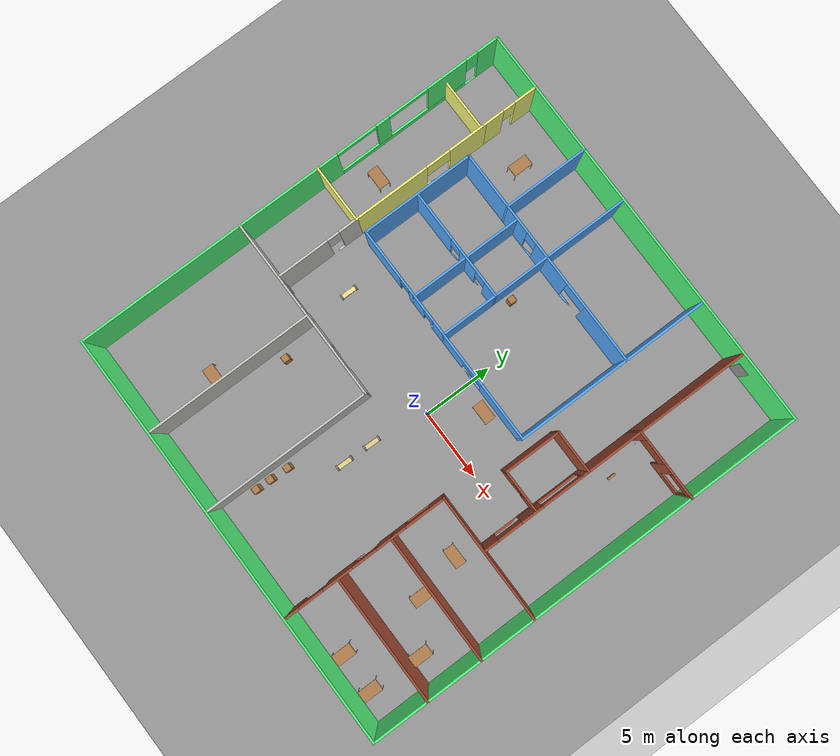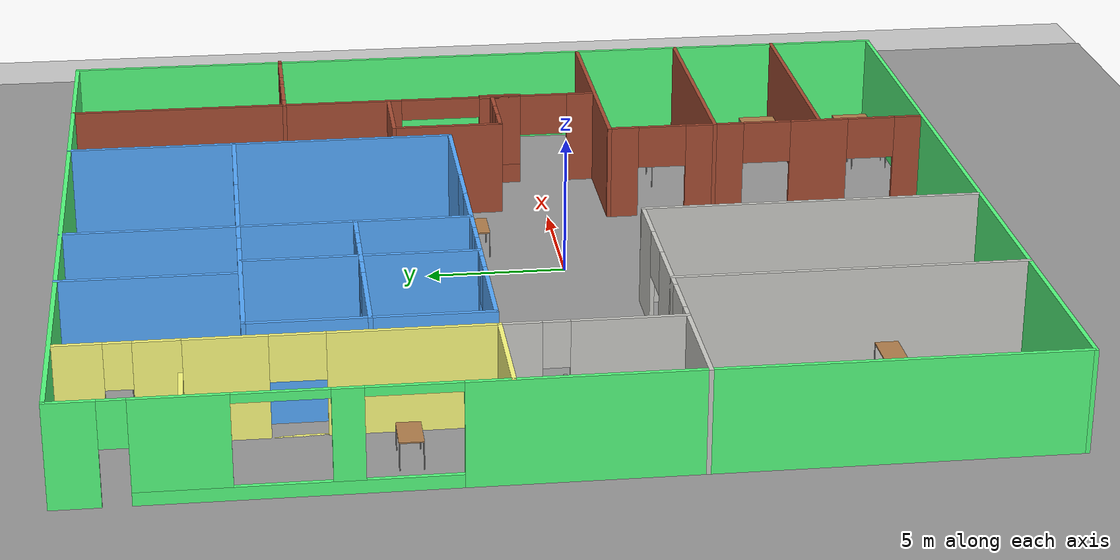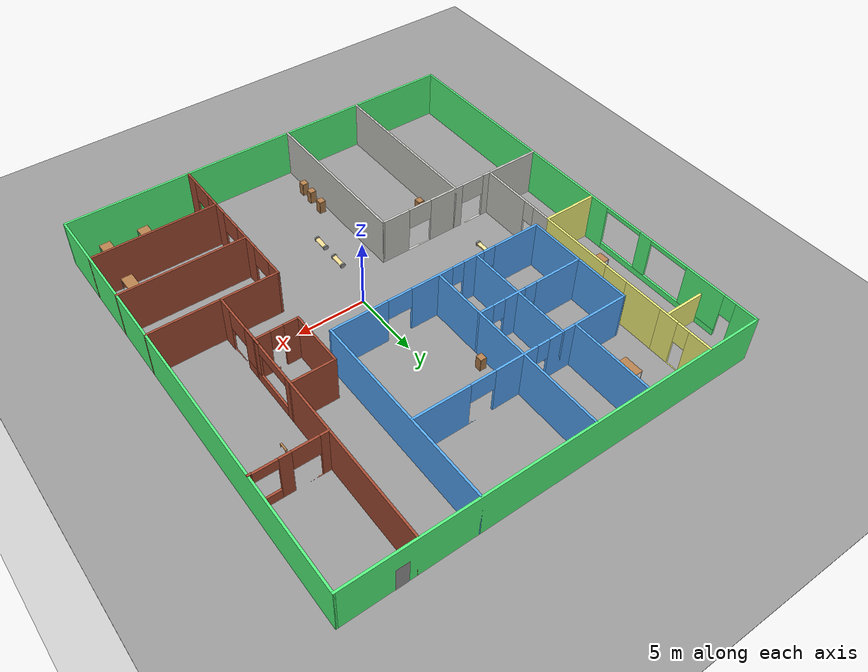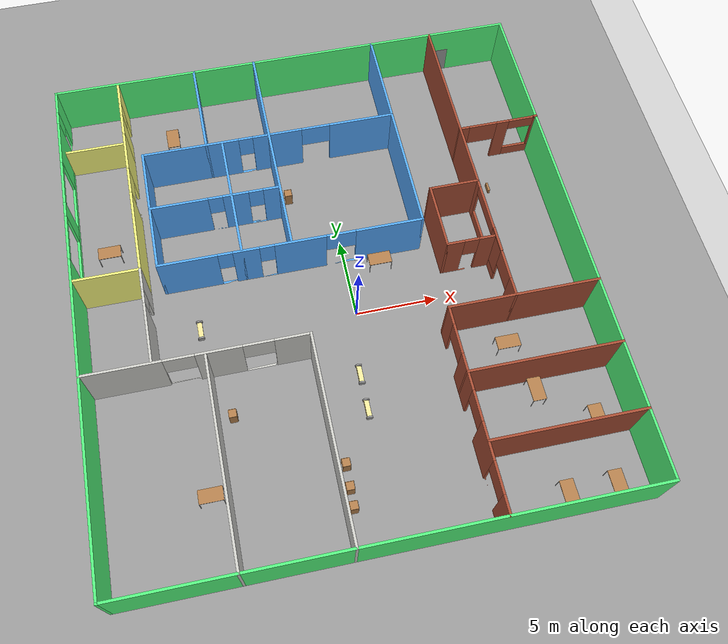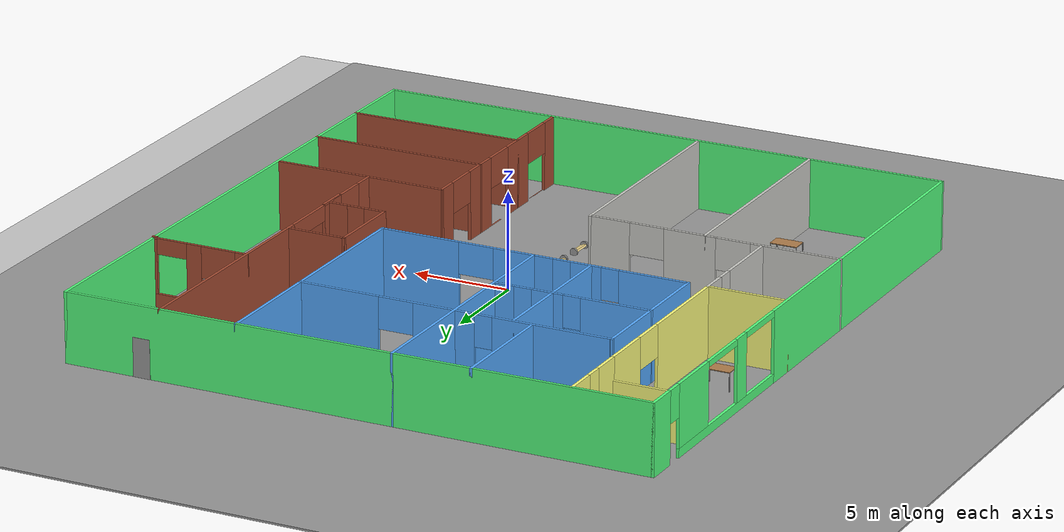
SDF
<sdf version="1.6">
 <world name="default">
  <plugin name="welcome" filename="libwelcome.so"/>
  <light name="sun" type="directional">
   <pose>0 0 10 0 -0 0</pose>
   <diffuse>0.8 0.8 0.8 1</diffuse>
   <specular>0.1 0.1 0.1 1</specular>
   <attenuation>
    <range>1000</range>
    <constant>0.9</constant>
    <linear>0.01</linear>
    <quadratic>0.001</quadratic>
   </attenuation>
   <direction>-0.5 0.5 -1</direction>
  </light>
  <model name="ground_plane">
   <static>1</static>
   <link name="link">
    <collision name="collision">
     <geometry><plane><normal>0 0 1</normal><size>100 100</size></plane></geometry>
     <surface><friction><ode><mu>100</mu><mu2>50</mu2></ode></friction></surface>
    </collision>
    <visual name="visual">
     <cast_shadows>0</cast_shadows>
     <geometry><plane><normal>0 0 1</normal><size>100 100</size></plane></geometry>
     <material>
      <script><uri>file://media/materials/scripts/gazebo.material</uri><name>Gazebo/Grey</name></script>
     </material>
    </visual>
   </link>
  </model>
  <gravity>0 0 -9.8</gravity>
  <magnetic_field>6e-06 2.3e-05 -4.2e-05</magnetic_field>
  <atmosphere type="adiabatic"/>
  <physics name="default_physics" default="0" type="ode">
   <max_step_size>0.001</max_step_size>
   <real_time_factor>1</real_time_factor>
   <real_time_update_rate>1000</real_time_update_rate>
  </physics>
  <scene><ambient>0.4 0.4 0.4 1</ambient><background>0.7 0.7 0.7 1</background><shadows>1</shadows></scene>
  <spherical_coordinates>
   <surface_model>EARTH_WGS84</surface_model>
   <latitude_deg>0</latitude_deg>
   <longitude_deg>0</longitude_deg>
   <elevation>0</elevation>
   <heading_deg>0</heading_deg>
  </spherical_coordinates>
  <model name="myfloorplan">
   <pose>-1.20922 1.7115 0 0 -0 0</pose>
   <link name="Door_22">
    <collision name="Door_22_Collision">
     <geometry><box><size>0.9 0.17 2</size></box></geometry>
     <pose>0 0 1 0 -0 0</pose>
    </collision>
    <visual name="Door_22_Visual">
     <pose>0 0 1 0 -0 0</pose>
     <geometry><box><size>0.9 0.17 2</size></box></geometry>
     <material>
      <script><uri>file://media/materials/scripts/gazebo.material</uri><name>Gazebo/Grey</name></script>
     </material>
    </visual>
    <pose>11 16 0 0 -0 0</pose>
   </link>
   <link name="Wall_0">
    <collision name="Wall_0_Collision">
     <geometry><box><size>30.15 0.15 3.6</size></box></geometry>
     <pose>0 0 1.8 0 -0 0</pose>
    </collision>
    <visual name="Wall_0_Visual">
     <pose>0 0 1.8 0 -0 0</pose>
     <geometry><box><size>30.15 0.15 3.6</size></box></geometry>
     <material>
      <script><uri>file://media/materials/scripts/gazebo.material</uri><name>Gazebo/Grey</name></script>
      <ambient>0.333333 1 0.498039 1</ambient>
     </material>
    </visual>
    <pose>0 16 0 0 -0 0</pose>
   </link>
   <link name="Wall_13">
    <collision name="Wall_13_Collision">
     <geometry><box><size>12.15 0.15 3.6</size></box></geometry>
     <pose>0 0 1.8 0 -0 0</pose>
    </collision>
    <visual name="Wall_13_Visual">
     <pose>0 0 1.8 0 -0 0</pose>
     <geometry><box><size>12.15 0.15 3.6</size></box></geometry>
     <material>
      <script><uri>file://media/materials/scripts/gazebo.material</uri><name>Gazebo/CeilingTiled</name></script>
      <ambient>1 1 0.498039 1</ambient>
     </material>
    </visual>
    <pose>-8 -10 0 0 0 -1.5708</pose>
   </link>
   <link name="Wall_15">
    <collision name="Wall_15_Collision">
     <geometry><box><size>12.15 0.15 3.6</size></box></geometry>
     <pose>0 0 1.8 0 -0 0</pose>
    </collision>
    <visual name="Wall_15_Visual">
     <pose>0 0 1.8 0 -0 0</pose>
     <geometry><box><size>12.15 0.15 3.6</size></box></geometry>
     <material>
      <script><uri>file://media/materials/scripts/gazebo.material</uri><name>Gazebo/CeilingTiled</name></script>
      <ambient>1 1 0.498039 1</ambient>
     </material>
    </visual>
    <pose>-2 -10 0 0 0 -1.5708</pose>
   </link>
   <link name="Wall_17">
    <collision name="Wall_17_Collision">
     <geometry><box><size>9.15 0.15 3.6</size></box></geometry>
     <pose>0 0 1.8 0 -0 0</pose>
    </collision>
    <visual name="Wall_17_Visual">
     <pose>0 0 1.8 0 -0 0</pose>
     <geometry><box><size>9.15 0.15 3.6</size></box></geometry>
     <material>
      <script><uri>file://media/materials/scripts/gazebo.material</uri><name>Gazebo/Bricks</name></script>
      <ambient>0.333333 0.666667 1 1</ambient>
     </material>
    </visual>
    <pose>10.5 -4 0 0 -0 0</pose>
   </link>
   <link name="Wall_19">
    <collision name="Wall_19_Collision">
     <geometry><box><size>9.15 0.15 3.6</size></box></geometry>
     <pose>0 0 1.8 0 -0 0</pose>
    </collision>
    <visual name="Wall_19_Visual">
     <pose>0 0 1.8 0 -0 0</pose>
     <geometry><box><size>9.15 0.15 3.6</size></box></geometry>
     <material>
      <script><uri>file://media/materials/scripts/gazebo.material</uri><name>Gazebo/Bricks</name></script>
      <ambient>0.333333 0.666667 1 1</ambient>
     </material>
    </visual>
    <pose>10.5 -8 0 0 -0 0</pose>
   </link>
   <link name="Wall_21">
    <collision name="Wall_21_Collision">
     <geometry><box><size>9.15 0.15 3.6</size></box></geometry>
     <pose>0 0 1.8 0 -0 0</pose>
    </collision>
    <visual name="Wall_21_Visual">
     <pose>0 0 1.8 0 -0 0</pose>
     <geometry><box><size>9.15 0.15 3.6</size></box></geometry>
     <material>
      <script><uri>file://media/materials/scripts/gazebo.material</uri><name>Gazebo/Bricks</name></script>
      <ambient>0.333333 0.666667 1 1</ambient>
     </material>
    </visual>
    <pose>10.5 -12 0 0 -0 0</pose>
   </link>
   <link name="Wall_23">
    <pose>10 6 0 0 0 -1.5708</pose>
    <visual name="Wall_23_Visual_0">
     <pose>-3.7875 0 1.8 0 -0 0</pose>
     <geometry><box><size>12.575 0.15 3.6</size></box></geometry>
     <material>
      <script><uri>file://media/materials/scripts/gazebo.material</uri><name>Gazebo/Bricks</name></script>
      <ambient>0.333333 0.666667 1 1</ambient>
     </material>
    </visual>
    <collision name="Wall_23_Collision_0">
     <geometry><box><size>12.575 0.15 3.6</size></box></geometry>
     <pose>-3.7875 0 1.8 0 -0 0</pose>
    </collision>
    <visual name="Wall_23_Visual_1">
     <pose>9.4875 0 1.8 0 -0 0</pose>
     <geometry><box><size>1.175 0.15 3.6</size></box></geometry>
     <material>
      <script><uri>file://media/materials/scripts/gazebo.material</uri><name>Gazebo/Bricks</name></script>
      <ambient>0.333333 0.666667 1 1</ambient>
     </material>
    </visual>
    <collision name="Wall_23_Collision_1">
     <geometry><box><size>1.175 0.15 3.6</size></box></geometry>
     <pose>9.4875 0 1.8 0 -0 0</pose>
    </collision>
    <visual name="Wall_23_Visual_2">
     <pose>4.8 0 0.4 0 -0 0</pose>
     <geometry><box><size>4.6 0.15 0.8</size></box></geometry>
     <material>
      <script><uri>file://media/materials/scripts/gazebo.material</uri><name>Gazebo/Bricks</name></script>
      <ambient>0.333333 0.666667 1 1</ambient>
     </material>
    </visual>
    <collision name="Wall_23_Collision_2">
     <geometry><box><size>4.6 0.15 0.8</size></box></geometry>
     <pose>4.8 0 0.4 0 -0 0</pose>
    </collision>
    <visual name="Wall_23_Visual_3">
     <pose>8 0 0 0 -0 0</pose>
     <geometry><box><size>1.8 0.15 0.1</size></box></geometry>
     <material>
      <script><uri>file://media/materials/scripts/gazebo.material</uri><name>Gazebo/Bricks</name></script>
      <ambient>0.333333 0.666667 1 1</ambient>
     </material>
    </visual>
    <collision name="Wall_23_Collision_3">
     <geometry><box><size>1.8 0.15 0.1</size></box></geometry>
     <pose>8 0 0 0 -0 0</pose>
    </collision>
    <visual name="Wall_23_Visual_4">
     <pose>6.3 0 2.2 0 -0 0</pose>
     <geometry><box><size>1.6 0.15 2.8</size></box></geometry>
     <material>
      <script><uri>file://media/materials/scripts/gazebo.material</uri><name>Gazebo/Bricks</name></script>
      <ambient>0.333333 0.666667 1 1</ambient>
     </material>
    </visual>
    <collision name="Wall_23_Collision_4">
     <geometry><box><size>1.6 0.15 2.8</size></box></geometry>
     <pose>6.3 0 2.2 0 -0 0</pose>
    </collision>
    <visual name="Wall_23_Visual_5">
     <pose>8 0 2.8 0 -0 0</pose>
     <geometry><box><size>1.8 0.15 1.6</size></box></geometry>
     <material>
      <script><uri>file://media/materials/scripts/gazebo.material</uri><name>Gazebo/Bricks</name></script>
      <ambient>0.333333 0.666667 1 1</ambient>
     </material>
    </visual>
    <collision name="Wall_23_Collision_5">
     <geometry><box><size>1.8 0.15 1.6</size></box></geometry>
     <pose>8 0 2.8 0 -0 0</pose>
    </collision>
    <visual name="Wall_23_Visual_6">
     <pose>4 0 3.2 0 -0 0</pose>
     <geometry><box><size>3 0.15 0.8</size></box></geometry>
     <material>
      <script><uri>file://media/materials/scripts/gazebo.material</uri><name>Gazebo/Bricks</name></script>
      <ambient>0.333333 0.666667 1 1</ambient>
     </material>
    </visual>
    <collision name="Wall_23_Collision_6">
     <geometry><box><size>3 0.15 0.8</size></box></geometry>
     <pose>4 0 3.2 0 -0 0</pose>
    </collision>
    <visual name="Wall_23_Visual_7">
     <pose>6.3 0 3.6 0 -0 0</pose>
     <geometry><box><size>1.6 0.15 0.1</size></box></geometry>
     <material>
      <script><uri>file://media/materials/scripts/gazebo.material</uri><name>Gazebo/Bricks</name></script>
      <ambient>0.333333 0.666667 1 1</ambient>
     </material>
    </visual>
    <collision name="Wall_23_Collision_7">
     <geometry><box><size>1.6 0.15 0.1</size></box></geometry>
     <pose>6.3 0 3.6 0 -0 0</pose>
    </collision>
   </link>
   <link name="Wall_25">
    <collision name="Wall_25_Collision">
     <geometry><box><size>6.15 0.15 3.6</size></box></geometry>
     <pose>0 0 1.8 0 -0 0</pose>
    </collision>
    <visual name="Wall_25_Visual">
     <pose>0 0 1.8 0 -0 0</pose>
     <geometry><box><size>6.15 0.15 3.6</size></box></geometry>
     <material>
      <script><uri>file://media/materials/scripts/gazebo.material</uri><name>Gazebo/Grey</name></script>
      <ambient>0.333333 0.666667 1 1</ambient>
     </material>
    </visual>
    <pose>-6 13 0 0 0 -1.5708</pose>
   </link>
   <link name="Wall_27">
    <collision name="Wall_27_Collision">
     <geometry><box><size>8.15 0.15 3.6</size></box></geometry>
     <pose>0 0 1.8 0 -0 0</pose>
    </collision>
    <visual name="Wall_27_Visual">
     <pose>0 0 1.8 0 -0 0</pose>
     <geometry><box><size>8.15 0.15 3.6</size></box></geometry>
     <material>
      <script><uri>file://media/materials/scripts/gazebo.material</uri><name>Gazebo/Grey</name></script>
      <ambient>0.333333 0.666667 1 1</ambient>
     </material>
    </visual>
    <pose>-10 6 0 0 0 -1.5708</pose>
   </link>
   <link name="Wall_29">
    <collision name="Wall_29_Collision">
     <geometry><box><size>14.15 0.15 3.6</size></box></geometry>
     <pose>0 0 1.8 0 -0 0</pose>
    </collision>
    <visual name="Wall_29_Visual">
     <pose>0 0 1.8 0 -0 0</pose>
     <geometry><box><size>14.15 0.15 3.6</size></box></geometry>
     <material>
      <script><uri>file://media/materials/scripts/gazebo.material</uri><name>Gazebo/Grey</name></script>
      <ambient>0.333333 0.666667 1 1</ambient>
     </material>
    </visual>
    <pose>-2 9 0 0 0 -1.5708</pose>
   </link>
   <link name="Wall_31">
    <collision name="Wall_31_Collision">
     <geometry><box><size>8.15 0.15 3.6</size></box></geometry>
     <pose>0 0 1.8 0 -0 0</pose>
    </collision>
    <visual name="Wall_31_Visual">
     <pose>0 0 1.8 0 -0 0</pose>
     <geometry><box><size>8.15 0.15 3.6</size></box></geometry>
     <material>
      <script><uri>file://media/materials/scripts/gazebo.material</uri><name>Gazebo/Grey</name></script>
      <ambient>0.333333 0.666667 1 1</ambient>
     </material>
    </visual>
    <pose>-5 6 0 0 0 -1.5708</pose>
   </link>
   <link name="Wall_33">
    <collision name="Wall_33_Collision">
     <geometry><box><size>3.15 0.15 3.6</size></box></geometry>
     <pose>0 0 1.8 0 -0 0</pose>
    </collision>
    <visual name="Wall_33_Visual">
     <pose>0 0 1.8 0 -0 0</pose>
     <geometry><box><size>3.15 0.15 3.6</size></box></geometry>
     <material>
      <script><uri>file://media/materials/scripts/gazebo.material</uri><name>Gazebo/Bricks</name></script>
      <ambient>0.333333 0.666667 1 1</ambient>
     </material>
    </visual>
    <pose>8.5 4 0 0 -0 3.14159</pose>
   </link>
   <link name="Wall_34">
    <collision name="Wall_34_Collision">
     <geometry><box><size>4.15 0.15 3.6</size></box></geometry>
     <pose>0 0 1.8 0 -0 0</pose>
    </collision>
    <visual name="Wall_34_Visual">
     <pose>0 0 1.8 0 -0 0</pose>
     <geometry><box><size>4.15 0.15 3.6</size></box></geometry>
     <material>
      <script><uri>file://media/materials/scripts/gazebo.material</uri><name>Gazebo/Bricks</name></script>
      <ambient>0.333333 0.666667 1 1</ambient>
     </material>
    </visual>
    <pose>7 2 0 0 0 -1.5708</pose>
   </link>
   <link name="Wall_36">
    <pose>-11 14 0 0 -0 1.5708</pose>
    <visual name="Wall_36_Visual_0">
     <pose>-1.30968 0 1.8 0 -0 0</pose>
     <geometry><box><size>1.53063 0.15 3.6</size></box></geometry>
     <material>
      <script><uri>file://media/materials/scripts/gazebo.material</uri><name>Gazebo/Grey</name></script>
      <ambient>1 1 0.498039 1</ambient>
     </material>
    </visual>
    <collision name="Wall_36_Collision_0">
     <geometry><box><size>1.53063 0.15 3.6</size></box></geometry>
     <pose>-1.30968 0 1.8 0 -0 0</pose>
    </collision>
    <visual name="Wall_36_Visual_1">
     <pose>1.21531 0 1.8 0 -0 0</pose>
     <geometry><box><size>1.71937 0.15 3.6</size></box></geometry>
     <material>
      <script><uri>file://media/materials/scripts/gazebo.material</uri><name>Gazebo/Grey</name></script>
      <ambient>1 1 0.498039 1</ambient>
     </material>
    </visual>
    <collision name="Wall_36_Collision_1">
     <geometry><box><size>1.71937 0.15 3.6</size></box></geometry>
     <pose>1.21531 0 1.8 0 -0 0</pose>
    </collision>
    <visual name="Wall_36_Visual_2">
     <pose>-0.09437 0 0 0 -0 0</pose>
     <geometry><box><size>0.9 0.15 0.1</size></box></geometry>
     <material>
      <script><uri>file://media/materials/scripts/gazebo.material</uri><name>Gazebo/Grey</name></script>
      <ambient>1 1 0.498039 1</ambient>
     </material>
    </visual>
    <collision name="Wall_36_Collision_2">
     <geometry><box><size>0.9 0.15 0.1</size></box></geometry>
     <pose>-0.09437 0 0 0 -0 0</pose>
    </collision>
    <visual name="Wall_36_Visual_3">
     <pose>-0.09437 0 2.8 0 -0 0</pose>
     <geometry><box><size>0.9 0.15 1.6</size></box></geometry>
     <material>
      <script><uri>file://media/materials/scripts/gazebo.material</uri><name>Gazebo/Grey</name></script>
      <ambient>1 1 0.498039 1</ambient>
     </material>
    </visual>
    <collision name="Wall_36_Collision_3">
     <geometry><box><size>0.9 0.15 1.6</size></box></geometry>
     <pose>-0.09437 0 2.8 0 -0 0</pose>
    </collision>
   </link>
   <link name="Wall_38">
    <pose>-11 7 0 0 0 -1.5708</pose>
    <visual name="Wall_38_Visual_0">
     <pose>-3.66056 0 1.8 0 -0 0</pose>
     <geometry><box><size>2.82888 0.15 3.6</size></box></geometry>
     <material>
      <script><uri>file://media/materials/scripts/gazebo.material</uri><name>Gazebo/Grey</name></script>
      <ambient>1 1 0.498039 1</ambient>
     </material>
    </visual>
    <collision name="Wall_38_Collision_0">
     <geometry><box><size>2.82888 0.15 3.6</size></box></geometry>
     <pose>-3.66056 0 1.8 0 -0 0</pose>
    </collision>
    <visual name="Wall_38_Visual_1">
     <pose>2.31444 0 1.8 0 -0 0</pose>
     <geometry><box><size>5.52112 0.15 3.6</size></box></geometry>
     <material>
      <script><uri>file://media/materials/scripts/gazebo.material</uri><name>Gazebo/Grey</name></script>
      <ambient>1 1 0.498039 1</ambient>
     </material>
    </visual>
    <collision name="Wall_38_Collision_1">
     <geometry><box><size>5.52112 0.15 3.6</size></box></geometry>
     <pose>2.31444 0 1.8 0 -0 0</pose>
    </collision>
    <visual name="Wall_38_Visual_2">
     <pose>-1.34612 0 0 0 -0 0</pose>
     <geometry><box><size>1.8 0.15 0.1</size></box></geometry>
     <material>
      <script><uri>file://media/materials/scripts/gazebo.material</uri><name>Gazebo/Grey</name></script>
      <ambient>1 1 0.498039 1</ambient>
     </material>
    </visual>
    <collision name="Wall_38_Collision_2">
     <geometry><box><size>1.8 0.15 0.1</size></box></geometry>
     <pose>-1.34612 0 0 0 -0 0</pose>
    </collision>
    <visual name="Wall_38_Visual_3">
     <pose>-1.34612 0 2.8 0 -0 0</pose>
     <geometry><box><size>1.8 0.15 1.6</size></box></geometry>
     <material>
      <script><uri>file://media/materials/scripts/gazebo.material</uri><name>Gazebo/Grey</name></script>
      <ambient>1 1 0.498039 1</ambient>
     </material>
    </visual>
    <collision name="Wall_38_Collision_3">
     <geometry><box><size>1.8 0.15 1.6</size></box></geometry>
     <pose>-1.34612 0 2.8 0 -0 0</pose>
    </collision>
   </link>
   <link name="Wall_39">
    <collision name="Wall_39_Collision">
     <geometry><box><size>4.15 0.15 3.6</size></box></geometry>
     <pose>0 0 1.8 0 -0 0</pose>
    </collision>
    <visual name="Wall_39_Visual">
     <pose>0 0 1.8 0 -0 0</pose>
     <geometry><box><size>4.15 0.15 3.6</size></box></geometry>
     <material>
      <script><uri>file://media/materials/scripts/gazebo.material</uri><name>Gazebo/Grey</name></script>
      <ambient>1 1 0.498039 1</ambient>
     </material>
    </visual>
    <pose>-13 2 0 0 -0 3.14159</pose>
   </link>
   <link name="Wall_41">
    <pose>-11 -0.999999 0 0 0 -1.5708</pose>
    <visual name="Wall_41_Visual_0">
     <pose>-2.36537 0 1.8 0 -0 0</pose>
     <geometry><box><size>1.41927 0.15 3.6</size></box></geometry>
     <material>
      <script><uri>file://media/materials/scripts/gazebo.material</uri><name>Gazebo/CeilingTiled</name></script>
      <ambient>1 1 0.498039 1</ambient>
     </material>
    </visual>
    <collision name="Wall_41_Collision_0">
     <geometry><box><size>1.41927 0.15 3.6</size></box></geometry>
     <pose>-2.36537 0 1.8 0 -0 0</pose>
    </collision>
    <visual name="Wall_41_Visual_1">
     <pose>1.15963 0 1.8 0 -0 0</pose>
     <geometry><box><size>3.83073 0.15 3.6</size></box></geometry>
     <material>
      <script><uri>file://media/materials/scripts/gazebo.material</uri><name>Gazebo/CeilingTiled</name></script>
      <ambient>1 1 0.498039 1</ambient>
     </material>
    </visual>
    <collision name="Wall_41_Collision_1">
     <geometry><box><size>3.83073 0.15 3.6</size></box></geometry>
     <pose>1.15963 0 1.8 0 -0 0</pose>
    </collision>
    <visual name="Wall_41_Visual_2">
     <pose>-1.20573 0 0 0 -0 0</pose>
     <geometry><box><size>0.9 0.15 0.1</size></box></geometry>
     <material>
      <script><uri>file://media/materials/scripts/gazebo.material</uri><name>Gazebo/CeilingTiled</name></script>
      <ambient>1 1 0.498039 1</ambient>
     </material>
    </visual>
    <collision name="Wall_41_Collision_2">
     <geometry><box><size>0.9 0.15 0.1</size></box></geometry>
     <pose>-1.20573 0 0 0 -0 0</pose>
    </collision>
    <visual name="Wall_41_Visual_3">
     <pose>-1.20573 0 2.8 0 -0 0</pose>
     <geometry><box><size>0.9 0.15 1.6</size></box></geometry>
     <material>
      <script><uri>file://media/materials/scripts/gazebo.material</uri><name>Gazebo/CeilingTiled</name></script>
      <ambient>1 1 0.498039 1</ambient>
     </material>
    </visual>
    <collision name="Wall_41_Collision_3">
     <geometry><box><size>0.9 0.15 1.6</size></box></geometry>
     <pose>-1.20573 0 2.8 0 -0 0</pose>
    </collision>
   </link>
   <link name="Wall_44">
    <pose>-8.5 -4 0 0 -0 0</pose>
    <visual name="Wall_44_Visual_0">
     <pose>-4.2375 0 1.8 0 -0 0</pose>
     <geometry><box><size>4.675 0.15 3.6</size></box></geometry>
     <material>
      <script><uri>file://media/materials/scripts/gazebo.material</uri><name>Gazebo/CeilingTiled</name></script>
      <ambient>1 1 0.498039 1</ambient>
     </material>
    </visual>
    <collision name="Wall_44_Collision_0">
     <geometry><box><size>4.675 0.15 3.6</size></box></geometry>
     <pose>-4.2375 0 1.8 0 -0 0</pose>
    </collision>
    <visual name="Wall_44_Visual_1">
     <pose>1.25 0 1.8 0 -0 0</pose>
     <geometry><box><size>2.7 0.15 3.6</size></box></geometry>
     <material>
      <script><uri>file://media/materials/scripts/gazebo.material</uri><name>Gazebo/CeilingTiled</name></script>
      <ambient>1 1 0.498039 1</ambient>
     </material>
    </visual>
    <collision name="Wall_44_Collision_1">
     <geometry><box><size>2.7 0.15 3.6</size></box></geometry>
     <pose>1.25 0 1.8 0 -0 0</pose>
    </collision>
    <visual name="Wall_44_Visual_2">
     <pose>5.4875 0 1.8 0 -0 0</pose>
     <geometry><box><size>2.175 0.15 3.6</size></box></geometry>
     <material>
      <script><uri>file://media/materials/scripts/gazebo.material</uri><name>Gazebo/CeilingTiled</name></script>
      <ambient>1 1 0.498039 1</ambient>
     </material>
    </visual>
    <collision name="Wall_44_Collision_2">
     <geometry><box><size>2.175 0.15 3.6</size></box></geometry>
     <pose>5.4875 0 1.8 0 -0 0</pose>
    </collision>
    <visual name="Wall_44_Visual_3">
     <pose>-1 0 0 0 -0 0</pose>
     <geometry><box><size>1.8 0.15 0.1</size></box></geometry>
     <material>
      <script><uri>file://media/materials/scripts/gazebo.material</uri><name>Gazebo/CeilingTiled</name></script>
      <ambient>1 1 0.498039 1</ambient>
     </material>
    </visual>
    <collision name="Wall_44_Collision_3">
     <geometry><box><size>1.8 0.15 0.1</size></box></geometry>
     <pose>-1 0 0 0 -0 0</pose>
    </collision>
    <visual name="Wall_44_Visual_4">
     <pose>3.5 0 0 0 -0 0</pose>
     <geometry><box><size>1.8 0.15 0.1</size></box></geometry>
     <material>
      <script><uri>file://media/materials/scripts/gazebo.material</uri><name>Gazebo/CeilingTiled</name></script>
      <ambient>1 1 0.498039 1</ambient>
     </material>
    </visual>
    <collision name="Wall_44_Collision_4">
     <geometry><box><size>1.8 0.15 0.1</size></box></geometry>
     <pose>3.5 0 0 0 -0 0</pose>
    </collision>
    <visual name="Wall_44_Visual_5">
     <pose>-1 0 2.8 0 -0 0</pose>
     <geometry><box><size>1.8 0.15 1.6</size></box></geometry>
     <material>
      <script><uri>file://media/materials/scripts/gazebo.material</uri><name>Gazebo/CeilingTiled</name></script>
      <ambient>1 1 0.498039 1</ambient>
     </material>
    </visual>
    <collision name="Wall_44_Collision_5">
     <geometry><box><size>1.8 0.15 1.6</size></box></geometry>
     <pose>-1 0 2.8 0 -0 0</pose>
    </collision>
    <visual name="Wall_44_Visual_6">
     <pose>3.5 0 2.8 0 -0 0</pose>
     <geometry><box><size>1.8 0.15 1.6</size></box></geometry>
     <material>
      <script><uri>file://media/materials/scripts/gazebo.material</uri><name>Gazebo/CeilingTiled</name></script>
      <ambient>1 1 0.498039 1</ambient>
     </material>
    </visual>
    <collision name="Wall_44_Collision_6">
     <geometry><box><size>1.8 0.15 1.6</size></box></geometry>
     <pose>3.5 0 2.8 0 -0 0</pose>
    </collision>
   </link>
   <link name="Wall_46">
    <pose>6 -10 0 0 0 -1.5708</pose>
    <visual name="Wall_46_Visual_0">
     <pose>-5.4875 0 1.8 0 -0 0</pose>
     <geometry><box><size>1.175 0.15 3.6</size></box></geometry>
     <material>
      <script><uri>file://media/materials/scripts/gazebo.material</uri><name>Gazebo/Bricks</name></script>
      <ambient>0.333333 0.666667 1 1</ambient>
     </material>
    </visual>
    <collision name="Wall_46_Collision_0">
     <geometry><box><size>1.175 0.15 3.6</size></box></geometry>
     <pose>-5.4875 0 1.8 0 -0 0</pose>
    </collision>
    <visual name="Wall_46_Visual_1">
     <pose>-2 0 1.8 0 -0 0</pose>
     <geometry><box><size>2.2 0.15 3.6</size></box></geometry>
     <material>
      <script><uri>file://media/materials/scripts/gazebo.material</uri><name>Gazebo/Bricks</name></script>
      <ambient>0.333333 0.666667 1 1</ambient>
     </material>
    </visual>
    <collision name="Wall_46_Collision_1">
     <geometry><box><size>2.2 0.15 3.6</size></box></geometry>
     <pose>-2 0 1.8 0 -0 0</pose>
    </collision>
    <visual name="Wall_46_Visual_2">
     <pose>2 0 1.8 0 -0 0</pose>
     <geometry><box><size>2.2 0.15 3.6</size></box></geometry>
     <material>
      <script><uri>file://media/materials/scripts/gazebo.material</uri><name>Gazebo/Bricks</name></script>
      <ambient>0.333333 0.666667 1 1</ambient>
     </material>
    </visual>
    <collision name="Wall_46_Collision_2">
     <geometry><box><size>2.2 0.15 3.6</size></box></geometry>
     <pose>2 0 1.8 0 -0 0</pose>
    </collision>
    <visual name="Wall_46_Visual_3">
     <pose>5.4875 0 1.8 0 -0 0</pose>
     <geometry><box><size>1.175 0.15 3.6</size></box></geometry>
     <material>
      <script><uri>file://media/materials/scripts/gazebo.material</uri><name>Gazebo/Bricks</name></script>
      <ambient>0.333333 0.666667 1 1</ambient>
     </material>
    </visual>
    <collision name="Wall_46_Collision_3">
     <geometry><box><size>1.175 0.15 3.6</size></box></geometry>
     <pose>5.4875 0 1.8 0 -0 0</pose>
    </collision>
    <visual name="Wall_46_Visual_4">
     <pose>-4 0 0 0 -0 0</pose>
     <geometry><box><size>1.8 0.15 0.1</size></box></geometry>
     <material>
      <script><uri>file://media/materials/scripts/gazebo.material</uri><name>Gazebo/Bricks</name></script>
      <ambient>0.333333 0.666667 1 1</ambient>
     </material>
    </visual>
    <collision name="Wall_46_Collision_4">
     <geometry><box><size>1.8 0.15 0.1</size></box></geometry>
     <pose>-4 0 0 0 -0 0</pose>
    </collision>
    <visual name="Wall_46_Visual_5">
     <geometry><box><size>1.8 0.15 0.1</size></box></geometry>
     <material>
      <script><uri>file://media/materials/scripts/gazebo.material</uri><name>Gazebo/Bricks</name></script>
      <ambient>0.333333 0.666667 1 1</ambient>
     </material>
    </visual>
    <collision name="Wall_46_Collision_5"><geometry><box><size>1.8 0.15 0.1</size></box></geometry></collision>
    <visual name="Wall_46_Visual_6">
     <pose>4 0 0 0 -0 0</pose>
     <geometry><box><size>1.8 0.15 0.1</size></box></geometry>
     <material>
      <script><uri>file://media/materials/scripts/gazebo.material</uri><name>Gazebo/Bricks</name></script>
      <ambient>0.333333 0.666667 1 1</ambient>
     </material>
    </visual>
    <collision name="Wall_46_Collision_6">
     <geometry><box><size>1.8 0.15 0.1</size></box></geometry>
     <pose>4 0 0 0 -0 0</pose>
    </collision>
    <visual name="Wall_46_Visual_7">
     <pose>-4 0 2.8 0 -0 0</pose>
     <geometry><box><size>1.8 0.15 1.6</size></box></geometry>
     <material>
      <script><uri>file://media/materials/scripts/gazebo.material</uri><name>Gazebo/Bricks</name></script>
      <ambient>0.333333 0.666667 1 1</ambient>
     </material>
    </visual>
    <collision name="Wall_46_Collision_7">
     <geometry><box><size>1.8 0.15 1.6</size></box></geometry>
     <pose>-4 0 2.8 0 -0 0</pose>
    </collision>
    <visual name="Wall_46_Visual_8">
     <pose>-0 0 2.8 0 -0 0</pose>
     <geometry><box><size>1.8 0.15 1.6</size></box></geometry>
     <material>
      <script><uri>file://media/materials/scripts/gazebo.material</uri><name>Gazebo/Bricks</name></script>
      <ambient>0.333333 0.666667 1 1</ambient>
     </material>
    </visual>
    <collision name="Wall_46_Collision_8">
     <geometry><box><size>1.8 0.15 1.6</size></box></geometry>
     <pose>-0 0 2.8 0 -0 0</pose>
    </collision>
    <visual name="Wall_46_Visual_9">
     <pose>4 0 2.8 0 -0 0</pose>
     <geometry><box><size>1.8 0.15 1.6</size></box></geometry>
     <material>
      <script><uri>file://media/materials/scripts/gazebo.material</uri><name>Gazebo/Bricks</name></script>
      <ambient>0.333333 0.666667 1 1</ambient>
     </material>
    </visual>
    <collision name="Wall_46_Collision_9">
     <geometry><box><size>1.8 0.15 1.6</size></box></geometry>
     <pose>4 0 2.8 0 -0 0</pose>
    </collision>
   </link>
   <link name="Wall_48">
    <pose>12.5 8 0 0 -0 0</pose>
    <visual name="Wall_48_Visual_0">
     <pose>-2.2375 0 1.8 0 -0 0</pose>
     <geometry><box><size>0.675 0.15 3.6</size></box></geometry>
     <material>
      <script><uri>file://media/materials/scripts/gazebo.material</uri><name>Gazebo/Bricks</name></script>
      <ambient>0.333333 0.666667 1 1</ambient>
     </material>
    </visual>
    <collision name="Wall_48_Collision_0">
     <geometry><box><size>0.675 0.15 3.6</size></box></geometry>
     <pose>-2.2375 0 1.8 0 -0 0</pose>
    </collision>
    <visual name="Wall_48_Visual_1">
     <pose>0.3 0 1.8 0 -0 0</pose>
     <geometry><box><size>0.8 0.15 3.6</size></box></geometry>
     <material>
      <script><uri>file://media/materials/scripts/gazebo.material</uri><name>Gazebo/Bricks</name></script>
      <ambient>0.333333 0.666667 1 1</ambient>
     </material>
    </visual>
    <collision name="Wall_48_Collision_1">
     <geometry><box><size>0.8 0.15 3.6</size></box></geometry>
     <pose>0.3 0 1.8 0 -0 0</pose>
    </collision>
    <visual name="Wall_48_Visual_2">
     <pose>-1 0 0 0 -0 0</pose>
     <geometry><box><size>1.8 0.15 0.1</size></box></geometry>
     <material>
      <script><uri>file://media/materials/scripts/gazebo.material</uri><name>Gazebo/Bricks</name></script>
      <ambient>0.333333 0.666667 1 1</ambient>
     </material>
    </visual>
    <collision name="Wall_48_Collision_2">
     <geometry><box><size>1.8 0.15 0.1</size></box></geometry>
     <pose>-1 0 0 0 -0 0</pose>
    </collision>
    <visual name="Wall_48_Visual_3">
     <pose>1.6375 0 0.4 0 -0 0</pose>
     <geometry><box><size>1.875 0.15 0.8</size></box></geometry>
     <material>
      <script><uri>file://media/materials/scripts/gazebo.material</uri><name>Gazebo/Bricks</name></script>
      <ambient>0.333333 0.666667 1 1</ambient>
     </material>
    </visual>
    <collision name="Wall_48_Collision_3">
     <geometry><box><size>1.875 0.15 0.8</size></box></geometry>
     <pose>1.6375 0 0.4 0 -0 0</pose>
    </collision>
    <visual name="Wall_48_Visual_4">
     <pose>2.4375 0 2.2 0 -0 0</pose>
     <geometry><box><size>0.275 0.15 2.8</size></box></geometry>
     <material>
      <script><uri>file://media/materials/scripts/gazebo.material</uri><name>Gazebo/Bricks</name></script>
      <ambient>0.333333 0.666667 1 1</ambient>
     </material>
    </visual>
    <collision name="Wall_48_Collision_4">
     <geometry><box><size>0.275 0.15 2.8</size></box></geometry>
     <pose>2.4375 0 2.2 0 -0 0</pose>
    </collision>
    <visual name="Wall_48_Visual_5">
     <pose>-1 0 2.8 0 -0 0</pose>
     <geometry><box><size>1.8 0.15 1.6</size></box></geometry>
     <material>
      <script><uri>file://media/materials/scripts/gazebo.material</uri><name>Gazebo/Bricks</name></script>
      <ambient>0.333333 0.666667 1 1</ambient>
     </material>
    </visual>
    <collision name="Wall_48_Collision_5">
     <geometry><box><size>1.8 0.15 1.6</size></box></geometry>
     <pose>-1 0 2.8 0 -0 0</pose>
    </collision>
    <visual name="Wall_48_Visual_6">
     <pose>1.5 0 3.2 0 -0 0</pose>
     <geometry><box><size>1.6 0.15 0.8</size></box></geometry>
     <material>
      <script><uri>file://media/materials/scripts/gazebo.material</uri><name>Gazebo/Bricks</name></script>
      <ambient>0.333333 0.666667 1 1</ambient>
     </material>
    </visual>
    <collision name="Wall_48_Collision_6">
     <geometry><box><size>1.6 0.15 0.8</size></box></geometry>
     <pose>1.5 0 3.2 0 -0 0</pose>
    </collision>
    <visual name="Wall_48_Visual_7">
     <pose>2.4375 0 3.6 0 -0 0</pose>
     <geometry><box><size>0.275 0.15 0.1</size></box></geometry>
     <material>
      <script><uri>file://media/materials/scripts/gazebo.material</uri><name>Gazebo/Bricks</name></script>
      <ambient>0.333333 0.666667 1 1</ambient>
     </material>
    </visual>
    <collision name="Wall_48_Collision_7">
     <geometry><box><size>0.275 0.15 0.1</size></box></geometry>
     <pose>2.4375 0 3.6 0 -0 0</pose>
    </collision>
   </link>
   <link name="Wall_5">
    <collision name="Wall_5_Collision">
     <geometry><box><size>32.15 0.15 3.6</size></box></geometry>
     <pose>0 0 1.8 0 -0 0</pose>
    </collision>
    <visual name="Wall_5_Visual">
     <pose>0 0 1.8 0 -0 0</pose>
     <geometry><box><size>32.15 0.15 3.6</size></box></geometry>
     <material>
      <script><uri>file://media/materials/scripts/gazebo.material</uri><name>Gazebo/Grey</name></script>
      <ambient>0.333333 1 0.498039 1</ambient>
     </material>
    </visual>
    <pose>15 1e-06 0 0 0 -1.5708</pose>
   </link>
   <link name="Wall_50">
    <pose>8.5 1e-06 0 0 -0 0</pose>
    <visual name="Wall_50_Visual_0">
     <pose>-1.0125 0 1.8 0 -0 0</pose>
     <geometry><box><size>1.125 0.15 3.6</size></box></geometry>
     <material>
      <script><uri>file://media/materials/scripts/gazebo.material</uri><name>Gazebo/Bricks</name></script>
      <ambient>0.333333 0.666667 1 1</ambient>
     </material>
    </visual>
    <collision name="Wall_50_Collision_0">
     <geometry><box><size>1.125 0.15 3.6</size></box></geometry>
     <pose>-1.0125 0 1.8 0 -0 0</pose>
    </collision>
    <visual name="Wall_50_Visual_1">
     <pose>1.0125 0 1.8 0 -0 0</pose>
     <geometry><box><size>1.125 0.15 3.6</size></box></geometry>
     <material>
      <script><uri>file://media/materials/scripts/gazebo.material</uri><name>Gazebo/Bricks</name></script>
      <ambient>0.333333 0.666667 1 1</ambient>
     </material>
    </visual>
    <collision name="Wall_50_Collision_1">
     <geometry><box><size>1.125 0.15 3.6</size></box></geometry>
     <pose>1.0125 0 1.8 0 -0 0</pose>
    </collision>
    <visual name="Wall_50_Visual_2">
     <geometry><box><size>0.9 0.15 0.1</size></box></geometry>
     <material>
      <script><uri>file://media/materials/scripts/gazebo.material</uri><name>Gazebo/Bricks</name></script>
      <ambient>0.333333 0.666667 1 1</ambient>
     </material>
    </visual>
    <collision name="Wall_50_Collision_2"><geometry><box><size>0.9 0.15 0.1</size></box></geometry></collision>
    <visual name="Wall_50_Visual_3">
     <pose>0 0 2.8 0 -0 0</pose>
     <geometry><box><size>0.9 0.15 1.6</size></box></geometry>
     <material>
      <script><uri>file://media/materials/scripts/gazebo.material</uri><name>Gazebo/Bricks</name></script>
      <ambient>0.333333 0.666667 1 1</ambient>
     </material>
    </visual>
    <collision name="Wall_50_Collision_3">
     <geometry><box><size>0.9 0.15 1.6</size></box></geometry>
     <pose>0 0 2.8 0 -0 0</pose>
    </collision>
   </link>
   <link name="Wall_52">
    <collision name="Wall_52_Collision">
     <geometry><box><size>14.15 0.15 3.6</size></box></geometry>
     <pose>0 0 1.8 0 -0 0</pose>
    </collision>
    <visual name="Wall_52_Visual">
     <pose>0 0 1.8 0 -0 0</pose>
     <geometry><box><size>14.15 0.15 3.6</size></box></geometry>
     <material>
      <script><uri>file://media/materials/scripts/gazebo.material</uri><name>Gazebo/Grey</name></script>
      <ambient>0.333333 0.666667 1 1</ambient>
     </material>
    </visual>
    <pose>6 9 0 0 0 -1.5708</pose>
   </link>
   <link name="Wall_54">
    <pose>-2 2 0 0 -0 0</pose>
    <visual name="Wall_54_Visual_0">
     <pose>-6.2625 0 1.8 0 -0 0</pose>
     <geometry><box><size>3.625 0.15 3.6</size></box></geometry>
     <material>
      <script><uri>file://media/materials/scripts/gazebo.material</uri><name>Gazebo/Grey</name></script>
      <ambient>0.333333 0.666667 1 1</ambient>
     </material>
    </visual>
    <collision name="Wall_54_Collision_0">
     <geometry><box><size>3.625 0.15 3.6</size></box></geometry>
     <pose>-6.2625 0 1.8 0 -0 0</pose>
    </collision>
    <visual name="Wall_54_Visual_1">
     <pose>-2.75 0 1.8 0 -0 0</pose>
     <geometry><box><size>1.6 0.15 3.6</size></box></geometry>
     <material>
      <script><uri>file://media/materials/scripts/gazebo.material</uri><name>Gazebo/Grey</name></script>
      <ambient>0.333333 0.666667 1 1</ambient>
     </material>
    </visual>
    <collision name="Wall_54_Collision_1">
     <geometry><box><size>1.6 0.15 3.6</size></box></geometry>
     <pose>-2.75 0 1.8 0 -0 0</pose>
    </collision>
    <visual name="Wall_54_Visual_2">
     <pose>0.525 0 1.8 0 -0 0</pose>
     <geometry><box><size>3.15 0.15 3.6</size></box></geometry>
     <material>
      <script><uri>file://media/materials/scripts/gazebo.material</uri><name>Gazebo/Grey</name></script>
      <ambient>0.333333 0.666667 1 1</ambient>
     </material>
    </visual>
    <collision name="Wall_54_Collision_2">
     <geometry><box><size>3.15 0.15 3.6</size></box></geometry>
     <pose>0.525 0 1.8 0 -0 0</pose>
    </collision>
    <visual name="Wall_54_Visual_3">
     <pose>5.9875 0 1.8 0 -0 0</pose>
     <geometry><box><size>4.175 0.15 3.6</size></box></geometry>
     <material>
      <script><uri>file://media/materials/scripts/gazebo.material</uri><name>Gazebo/Grey</name></script>
      <ambient>0.333333 0.666667 1 1</ambient>
     </material>
    </visual>
    <collision name="Wall_54_Collision_3">
     <geometry><box><size>4.175 0.15 3.6</size></box></geometry>
     <pose>5.9875 0 1.8 0 -0 0</pose>
    </collision>
    <visual name="Wall_54_Visual_4">
     <pose>-4 0 0 0 -0 0</pose>
     <geometry><box><size>0.9 0.15 0.1</size></box></geometry>
     <material>
      <script><uri>file://media/materials/scripts/gazebo.material</uri><name>Gazebo/Grey</name></script>
      <ambient>0.333333 0.666667 1 1</ambient>
     </material>
    </visual>
    <collision name="Wall_54_Collision_4">
     <geometry><box><size>0.9 0.15 0.1</size></box></geometry>
     <pose>-4 0 0 0 -0 0</pose>
    </collision>
    <visual name="Wall_54_Visual_5">
     <pose>-1.5 0 0 0 -0 0</pose>
     <geometry><box><size>0.9 0.15 0.1</size></box></geometry>
     <material>
      <script><uri>file://media/materials/scripts/gazebo.material</uri><name>Gazebo/Grey</name></script>
      <ambient>0.333333 0.666667 1 1</ambient>
     </material>
    </visual>
    <collision name="Wall_54_Collision_5">
     <geometry><box><size>0.9 0.15 0.1</size></box></geometry>
     <pose>-1.5 0 0 0 -0 0</pose>
    </collision>
    <visual name="Wall_54_Visual_6">
     <pose>3 0 0 0 -0 0</pose>
     <geometry><box><size>1.8 0.15 0.1</size></box></geometry>
     <material>
      <script><uri>file://media/materials/scripts/gazebo.material</uri><name>Gazebo/Grey</name></script>
      <ambient>0.333333 0.666667 1 1</ambient>
     </material>
    </visual>
    <collision name="Wall_54_Collision_6">
     <geometry><box><size>1.8 0.15 0.1</size></box></geometry>
     <pose>3 0 0 0 -0 0</pose>
    </collision>
    <visual name="Wall_54_Visual_7">
     <pose>-4 0 2.8 0 -0 0</pose>
     <geometry><box><size>0.9 0.15 1.6</size></box></geometry>
     <material>
      <script><uri>file://media/materials/scripts/gazebo.material</uri><name>Gazebo/Grey</name></script>
      <ambient>0.333333 0.666667 1 1</ambient>
     </material>
    </visual>
    <collision name="Wall_54_Collision_7">
     <geometry><box><size>0.9 0.15 1.6</size></box></geometry>
     <pose>-4 0 2.8 0 -0 0</pose>
    </collision>
    <visual name="Wall_54_Visual_8">
     <pose>-1.5 0 2.8 0 -0 0</pose>
     <geometry><box><size>0.9 0.15 1.6</size></box></geometry>
     <material>
      <script><uri>file://media/materials/scripts/gazebo.material</uri><name>Gazebo/Grey</name></script>
      <ambient>0.333333 0.666667 1 1</ambient>
     </material>
    </visual>
    <collision name="Wall_54_Collision_8">
     <geometry><box><size>0.9 0.15 1.6</size></box></geometry>
     <pose>-1.5 0 2.8 0 -0 0</pose>
    </collision>
    <visual name="Wall_54_Visual_9">
     <pose>3 0 2.8 0 -0 0</pose>
     <geometry><box><size>1.8 0.15 1.6</size></box></geometry>
     <material>
      <script><uri>file://media/materials/scripts/gazebo.material</uri><name>Gazebo/Grey</name></script>
      <ambient>0.333333 0.666667 1 1</ambient>
     </material>
    </visual>
    <collision name="Wall_54_Collision_9">
     <geometry><box><size>1.8 0.15 1.6</size></box></geometry>
     <pose>3 0 2.8 0 -0 0</pose>
    </collision>
   </link>
   <link name="Wall_56">
    <pose>-2 10 0 0 -0 0</pose>
    <visual name="Wall_56_Visual_0">
     <pose>-5.0125 0 1.8 0 -0 0</pose>
     <geometry><box><size>6.125 0.15 3.6</size></box></geometry>
     <material>
      <script><uri>file://media/materials/scripts/gazebo.material</uri><name>Gazebo/Grey</name></script>
      <ambient>0.333333 0.666667 1 1</ambient>
     </material>
    </visual>
    <collision name="Wall_56_Collision_0">
     <geometry><box><size>6.125 0.15 3.6</size></box></geometry>
     <pose>-5.0125 0 1.8 0 -0 0</pose>
    </collision>
    <visual name="Wall_56_Visual_1">
     <pose>0.525 0 1.8 0 -0 0</pose>
     <geometry><box><size>3.15 0.15 3.6</size></box></geometry>
     <material>
      <script><uri>file://media/materials/scripts/gazebo.material</uri><name>Gazebo/Grey</name></script>
      <ambient>0.333333 0.666667 1 1</ambient>
     </material>
    </visual>
    <collision name="Wall_56_Collision_1">
     <geometry><box><size>3.15 0.15 3.6</size></box></geometry>
     <pose>0.525 0 1.8 0 -0 0</pose>
    </collision>
    <visual name="Wall_56_Visual_2">
     <pose>5.9875 0 1.8 0 -0 0</pose>
     <geometry><box><size>4.175 0.15 3.6</size></box></geometry>
     <material>
      <script><uri>file://media/materials/scripts/gazebo.material</uri><name>Gazebo/Grey</name></script>
      <ambient>0.333333 0.666667 1 1</ambient>
     </material>
    </visual>
    <collision name="Wall_56_Collision_2">
     <geometry><box><size>4.175 0.15 3.6</size></box></geometry>
     <pose>5.9875 0 1.8 0 -0 0</pose>
    </collision>
    <visual name="Wall_56_Visual_3">
     <pose>-1.5 0 0 0 -0 0</pose>
     <geometry><box><size>0.9 0.15 0.1</size></box></geometry>
     <material>
      <script><uri>file://media/materials/scripts/gazebo.material</uri><name>Gazebo/Grey</name></script>
      <ambient>0.333333 0.666667 1 1</ambient>
     </material>
    </visual>
    <collision name="Wall_56_Collision_3">
     <geometry><box><size>0.9 0.15 0.1</size></box></geometry>
     <pose>-1.5 0 0 0 -0 0</pose>
    </collision>
    <visual name="Wall_56_Visual_4">
     <pose>3 0 0 0 -0 0</pose>
     <geometry><box><size>1.8 0.15 0.1</size></box></geometry>
     <material>
      <script><uri>file://media/materials/scripts/gazebo.material</uri><name>Gazebo/Grey</name></script>
      <ambient>0.333333 0.666667 1 1</ambient>
     </material>
    </visual>
    <collision name="Wall_56_Collision_4">
     <geometry><box><size>1.8 0.15 0.1</size></box></geometry>
     <pose>3 0 0 0 -0 0</pose>
    </collision>
    <visual name="Wall_56_Visual_5">
     <pose>-1.5 0 2.8 0 -0 0</pose>
     <geometry><box><size>0.9 0.15 1.6</size></box></geometry>
     <material>
      <script><uri>file://media/materials/scripts/gazebo.material</uri><name>Gazebo/Grey</name></script>
      <ambient>0.333333 0.666667 1 1</ambient>
     </material>
    </visual>
    <collision name="Wall_56_Collision_5">
     <geometry><box><size>0.9 0.15 1.6</size></box></geometry>
     <pose>-1.5 0 2.8 0 -0 0</pose>
    </collision>
    <visual name="Wall_56_Visual_6">
     <pose>3 0 2.8 0 -0 0</pose>
     <geometry><box><size>1.8 0.15 1.6</size></box></geometry>
     <material>
      <script><uri>file://media/materials/scripts/gazebo.material</uri><name>Gazebo/Grey</name></script>
      <ambient>0.333333 0.666667 1 1</ambient>
     </material>
    </visual>
    <collision name="Wall_56_Collision_6">
     <geometry><box><size>1.8 0.15 1.6</size></box></geometry>
     <pose>3 0 2.8 0 -0 0</pose>
    </collision>
   </link>
   <link name="Wall_58">
    <pose>-6 6 0 0 -0 0</pose>
    <visual name="Wall_58_Visual_0">
     <pose>-2.2625 0 1.8 0 -0 0</pose>
     <geometry><box><size>3.625 0.15 3.6</size></box></geometry>
     <material>
      <script><uri>file://media/materials/scripts/gazebo.material</uri><name>Gazebo/Grey</name></script>
      <ambient>0.333333 0.666667 1 1</ambient>
     </material>
    </visual>
    <collision name="Wall_58_Collision_0">
     <geometry><box><size>3.625 0.15 3.6</size></box></geometry>
     <pose>-2.2625 0 1.8 0 -0 0</pose>
    </collision>
    <visual name="Wall_58_Visual_1">
     <pose>1.25 0 1.8 0 -0 0</pose>
     <geometry><box><size>1.6 0.15 3.6</size></box></geometry>
     <material>
      <script><uri>file://media/materials/scripts/gazebo.material</uri><name>Gazebo/Grey</name></script>
      <ambient>0.333333 0.666667 1 1</ambient>
     </material>
    </visual>
    <collision name="Wall_58_Collision_1">
     <geometry><box><size>1.6 0.15 3.6</size></box></geometry>
     <pose>1.25 0 1.8 0 -0 0</pose>
    </collision>
    <visual name="Wall_58_Visual_2">
     <pose>3.5125 0 1.8 0 -0 0</pose>
     <geometry><box><size>1.125 0.15 3.6</size></box></geometry>
     <material>
      <script><uri>file://media/materials/scripts/gazebo.material</uri><name>Gazebo/Grey</name></script>
      <ambient>0.333333 0.666667 1 1</ambient>
     </material>
    </visual>
    <collision name="Wall_58_Collision_2">
     <geometry><box><size>1.125 0.15 3.6</size></box></geometry>
     <pose>3.5125 0 1.8 0 -0 0</pose>
    </collision>
    <visual name="Wall_58_Visual_3">
     <geometry><box><size>0.9 0.15 0.1</size></box></geometry>
     <material>
      <script><uri>file://media/materials/scripts/gazebo.material</uri><name>Gazebo/Grey</name></script>
      <ambient>0.333333 0.666667 1 1</ambient>
     </material>
    </visual>
    <collision name="Wall_58_Collision_3"><geometry><box><size>0.9 0.15 0.1</size></box></geometry></collision>
    <visual name="Wall_58_Visual_4">
     <pose>2.5 0 0 0 -0 0</pose>
     <geometry><box><size>0.9 0.15 0.1</size></box></geometry>
     <material>
      <script><uri>file://media/materials/scripts/gazebo.material</uri><name>Gazebo/Grey</name></script>
      <ambient>0.333333 0.666667 1 1</ambient>
     </material>
    </visual>
    <collision name="Wall_58_Collision_4">
     <geometry><box><size>0.9 0.15 0.1</size></box></geometry>
     <pose>2.5 0 0 0 -0 0</pose>
    </collision>
    <visual name="Wall_58_Visual_5">
     <pose>0 0 2.8 0 -0 0</pose>
     <geometry><box><size>0.9 0.15 1.6</size></box></geometry>
     <material>
      <script><uri>file://media/materials/scripts/gazebo.material</uri><name>Gazebo/Grey</name></script>
      <ambient>0.333333 0.666667 1 1</ambient>
     </material>
    </visual>
    <collision name="Wall_58_Collision_5">
     <geometry><box><size>0.9 0.15 1.6</size></box></geometry>
     <pose>0 0 2.8 0 -0 0</pose>
    </collision>
    <visual name="Wall_58_Visual_6">
     <pose>2.5 0 2.8 0 -0 0</pose>
     <geometry><box><size>0.9 0.15 1.6</size></box></geometry>
     <material>
      <script><uri>file://media/materials/scripts/gazebo.material</uri><name>Gazebo/Grey</name></script>
      <ambient>0.333333 0.666667 1 1</ambient>
     </material>
    </visual>
    <collision name="Wall_58_Collision_6">
     <geometry><box><size>0.9 0.15 1.6</size></box></geometry>
     <pose>2.5 0 2.8 0 -0 0</pose>
    </collision>
   </link>
   <link name="Wall_6">
    <collision name="Wall_6_Collision">
     <geometry><box><size>30.15 0.15 3.6</size></box></geometry>
     <pose>0 0 1.8 0 -0 0</pose>
    </collision>
    <visual name="Wall_6_Visual">
     <pose>0 0 1.8 0 -0 0</pose>
     <geometry><box><size>30.15 0.15 3.6</size></box></geometry>
     <material>
      <script><uri>file://media/materials/scripts/gazebo.material</uri><name>Gazebo/Grey</name></script>
      <ambient>0.333333 1 0.498039 1</ambient>
     </material>
    </visual>
    <pose>0 -16 0 0 -0 3.14159</pose>
   </link>
   <link name="Wall_7">
    <pose>-15 1e-06 0 0 -0 1.5708</pose>
    <visual name="Wall_7_Visual_0">
     <pose>-6.2875 0 1.8 0 -0 0</pose>
     <geometry><box><size>19.575 0.15 3.6</size></box></geometry>
     <material>
      <script><uri>file://media/materials/scripts/gazebo.material</uri><name>Gazebo/Grey</name></script>
      <ambient>0.333333 1 0.498039 1</ambient>
     </material>
    </visual>
    <collision name="Wall_7_Collision_0">
     <geometry><box><size>19.575 0.15 3.6</size></box></geometry>
     <pose>-6.2875 0 1.8 0 -0 0</pose>
    </collision>
    <visual name="Wall_7_Visual_1">
     <pose>15.2625 0 1.8 0 -0 0</pose>
     <geometry><box><size>1.625 0.15 3.6</size></box></geometry>
     <material>
      <script><uri>file://media/materials/scripts/gazebo.material</uri><name>Gazebo/Grey</name></script>
      <ambient>0.333333 1 0.498039 1</ambient>
     </material>
    </visual>
    <collision name="Wall_7_Collision_1">
     <geometry><box><size>1.625 0.15 3.6</size></box></geometry>
     <pose>15.2625 0 1.8 0 -0 0</pose>
    </collision>
    <visual name="Wall_7_Visual_2">
     <pose>8.525 0 0.25 0 -0 0</pose>
     <geometry><box><size>10.05 0.15 0.5</size></box></geometry>
     <material>
      <script><uri>file://media/materials/scripts/gazebo.material</uri><name>Gazebo/Grey</name></script>
      <ambient>0.333333 1 0.498039 1</ambient>
     </material>
    </visual>
    <collision name="Wall_7_Collision_2">
     <geometry><box><size>10.05 0.15 0.5</size></box></geometry>
     <pose>8.525 0 0.25 0 -0 0</pose>
    </collision>
    <visual name="Wall_7_Visual_3">
     <pose>14 0 0 0 -0 0</pose>
     <geometry><box><size>0.9 0.15 0.1</size></box></geometry>
     <material>
      <script><uri>file://media/materials/scripts/gazebo.material</uri><name>Gazebo/Grey</name></script>
      <ambient>0.333333 1 0.498039 1</ambient>
     </material>
    </visual>
    <collision name="Wall_7_Collision_3">
     <geometry><box><size>0.9 0.15 0.1</size></box></geometry>
     <pose>14 0 0 0 -0 0</pose>
    </collision>
    <visual name="Wall_7_Visual_4">
     <pose>7 0 2.05 0 -0 0</pose>
     <geometry><box><size>1 0.15 3.1</size></box></geometry>
     <material>
      <script><uri>file://media/materials/scripts/gazebo.material</uri><name>Gazebo/Grey</name></script>
      <ambient>0.333333 1 0.498039 1</ambient>
     </material>
    </visual>
    <collision name="Wall_7_Collision_4">
     <geometry><box><size>1 0.15 3.1</size></box></geometry>
     <pose>7 0 2.05 0 -0 0</pose>
    </collision>
    <visual name="Wall_7_Visual_5">
     <pose>12.025 0 2.05 0 -0 0</pose>
     <geometry><box><size>3.05 0.15 3.1</size></box></geometry>
     <material>
      <script><uri>file://media/materials/scripts/gazebo.material</uri><name>Gazebo/Grey</name></script>
      <ambient>0.333333 1 0.498039 1</ambient>
     </material>
    </visual>
    <collision name="Wall_7_Collision_5">
     <geometry><box><size>3.05 0.15 3.1</size></box></geometry>
     <pose>12.025 0 2.05 0 -0 0</pose>
    </collision>
    <visual name="Wall_7_Visual_6">
     <pose>14 0 2.8 0 -0 0</pose>
     <geometry><box><size>0.9 0.15 1.6</size></box></geometry>
     <material>
      <script><uri>file://media/materials/scripts/gazebo.material</uri><name>Gazebo/Grey</name></script>
      <ambient>0.333333 1 0.498039 1</ambient>
     </material>
    </visual>
    <collision name="Wall_7_Collision_6">
     <geometry><box><size>0.9 0.15 1.6</size></box></geometry>
     <pose>14 0 2.8 0 -0 0</pose>
    </collision>
    <visual name="Wall_7_Visual_7">
     <pose>5 0 3.45 0 -0 0</pose>
     <geometry><box><size>3 0.15 0.3</size></box></geometry>
     <material>
      <script><uri>file://media/materials/scripts/gazebo.material</uri><name>Gazebo/Grey</name></script>
      <ambient>0.333333 1 0.498039 1</ambient>
     </material>
    </visual>
    <collision name="Wall_7_Collision_7">
     <geometry><box><size>3 0.15 0.3</size></box></geometry>
     <pose>5 0 3.45 0 -0 0</pose>
    </collision>
    <visual name="Wall_7_Visual_8">
     <pose>9 0 3.45 0 -0 0</pose>
     <geometry><box><size>3 0.15 0.3</size></box></geometry>
     <material>
      <script><uri>file://media/materials/scripts/gazebo.material</uri><name>Gazebo/Grey</name></script>
      <ambient>0.333333 1 0.498039 1</ambient>
     </material>
    </visual>
    <collision name="Wall_7_Collision_8">
     <geometry><box><size>3 0.15 0.3</size></box></geometry>
     <pose>9 0 3.45 0 -0 0</pose>
    </collision>
   </link>
   <link name="Wall_9">
    <collision name="Wall_9_Collision">
     <geometry><box><size>4.15 0.15 2.5</size></box></geometry>
     <pose>0 0 1.25 0 -0 0</pose>
    </collision>
    <visual name="Wall_9_Visual">
     <pose>0 0 1.25 0 -0 0</pose>
     <geometry><box><size>4.15 0.15 2.5</size></box></geometry>
     <material>
      <script><uri>file://media/materials/scripts/gazebo.material</uri><name>Gazebo/Grey</name></script>
      <ambient>1 1 0.498039 1</ambient>
     </material>
    </visual>
    <pose>-13 12 0 0 -0 0</pose>
   </link>
   <static>1</static>
  </model>
  <model name="table_0_clone">
   <static>0</static>
   <link name="link">
    <collision name="surface">
     <pose>0 0 1 0 -0 0</pose>
     <geometry><box><size>1.5 0.8 0.03</size></box></geometry>
     <surface><friction><ode><mu>0.6</mu><mu2>0.6</mu2></ode></friction></surface>
    </collision>
    <visual name="visual1">
     <pose>0 0 1 0 -0 0</pose>
     <geometry><box><size>1.4 0.8 0.04</size></box></geometry>
     <material>
      <script><uri>file://media/materials/scripts/gazebo.material</uri><name>Gazebo/Wood</name></script>
     </material>
    </visual>
    <collision name="front_left_leg">
     <pose>0.68 0.38 0.5 0 -0 0</pose>
     <geometry><cylinder><radius>0.02</radius><length>1</length></cylinder></geometry>
    </collision>
    <visual name="front_left_leg">
     <pose>0.68 0.38 0.5 0 -0 0</pose>
     <geometry><cylinder><radius>0.02</radius><length>1</length></cylinder></geometry>
     <material>
      <script><uri>file://media/materials/scripts/gazebo.material</uri><name>Gazebo/Grey</name></script>
     </material>
    </visual>
    <collision name="front_right_leg">
     <pose>0.68 -0.38 0.5 0 -0 0</pose>
     <geometry><cylinder><radius>0.02</radius><length>1</length></cylinder></geometry>
    </collision>
    <visual name="front_right_leg">
     <pose>0.68 -0.38 0.5 0 -0 0</pose>
     <geometry><cylinder><radius>0.02</radius><length>1</length></cylinder></geometry>
     <material>
      <script><uri>file://media/materials/scripts/gazebo.material</uri><name>Gazebo/Grey</name></script>
     </material>
    </visual>
    <collision name="back_right_leg">
     <pose>-0.68 -0.38 0.5 0 -0 0</pose>
     <geometry><cylinder><radius>0.02</radius><length>1</length></cylinder></geometry>
    </collision>
    <visual name="back_right_leg">
     <pose>-0.68 -0.38 0.5 0 -0 0</pose>
     <geometry><cylinder><radius>0.02</radius><length>1</length></cylinder></geometry>
     <material>
      <script><uri>file://media/materials/scripts/gazebo.material</uri><name>Gazebo/Grey</name></script>
     </material>
    </visual>
    <collision name="back_left_leg">
     <pose>-0.68 0.38 0.5 0 -0 0</pose>
     <geometry><cylinder><radius>0.02</radius><length>1</length></cylinder></geometry>
    </collision>
    <visual name="back_left_leg">
     <pose>-0.68 0.38 0.5 0 -0 0</pose>
     <geometry><cylinder><radius>0.02</radius><length>1</length></cylinder></geometry>
     <material>
      <script><uri>file://media/materials/scripts/gazebo.material</uri><name>Gazebo/Grey</name></script>
     </material>
    </visual>
    <inertial>
     <inertia><ixx>1</ixx><ixy>0</ixy><ixz>0</ixz><iyy>1</iyy><iyz>0</iyz><izz>1</izz></inertia>
     <mass>1</mass>
    </inertial>
   </link>
   <pose>8.92902 -13.2599 -2e-06 0 -0 1.57</pose>
  </model>
  <model name="table_0_clone_0">
   <static>0</static>
   <link name="link">
    <collision name="surface">
     <pose>0 0 1 0 -0 0</pose>
     <geometry><box><size>1.5 0.8 0.03</size></box></geometry>
     <surface><friction><ode><mu>0.6</mu><mu2>0.6</mu2></ode></friction></surface>
    </collision>
    <visual name="visual1">
     <pose>0 0 1 0 -0 0</pose>
     <geometry><box><size>1.4 0.8 0.04</size></box></geometry>
     <material>
      <script><uri>file://media/materials/scripts/gazebo.material</uri><name>Gazebo/Wood</name></script>
     </material>
    </visual>
    <collision name="front_left_leg">
     <pose>0.68 0.38 0.5 0 -0 0</pose>
     <geometry><cylinder><radius>0.02</radius><length>1</length></cylinder></geometry>
    </collision>
    <visual name="front_left_leg">
     <pose>0.68 0.38 0.5 0 -0 0</pose>
     <geometry><cylinder><radius>0.02</radius><length>1</length></cylinder></geometry>
     <material>
      <script><uri>file://media/materials/scripts/gazebo.material</uri><name>Gazebo/Grey</name></script>
     </material>
    </visual>
    <collision name="front_right_leg">
     <pose>0.68 -0.38 0.5 0 -0 0</pose>
     <geometry><cylinder><radius>0.02</radius><length>1</length></cylinder></geometry>
    </collision>
    <visual name="front_right_leg">
     <pose>0.68 -0.38 0.5 0 -0 0</pose>
     <geometry><cylinder><radius>0.02</radius><length>1</length></cylinder></geometry>
     <material>
      <script><uri>file://media/materials/scripts/gazebo.material</uri><name>Gazebo/Grey</name></script>
     </material>
    </visual>
    <collision name="back_right_leg">
     <pose>-0.68 -0.38 0.5 0 -0 0</pose>
     <geometry><cylinder><radius>0.02</radius><length>1</length></cylinder></geometry>
    </collision>
    <visual name="back_right_leg">
     <pose>-0.68 -0.38 0.5 0 -0 0</pose>
     <geometry><cylinder><radius>0.02</radius><length>1</length></cylinder></geometry>
     <material>
      <script><uri>file://media/materials/scripts/gazebo.material</uri><name>Gazebo/Grey</name></script>
     </material>
    </visual>
    <collision name="back_left_leg">
     <pose>-0.68 0.38 0.5 0 -0 0</pose>
     <geometry><cylinder><radius>0.02</radius><length>1</length></cylinder></geometry>
    </collision>
    <visual name="back_left_leg">
     <pose>-0.68 0.38 0.5 0 -0 0</pose>
     <geometry><cylinder><radius>0.02</radius><length>1</length></cylinder></geometry>
     <material>
      <script><uri>file://media/materials/scripts/gazebo.material</uri><name>Gazebo/Grey</name></script>
     </material>
    </visual>
    <inertial>
     <inertia><ixx>1</ixx><ixy>0</ixy><ixz>0</ixz><iyy>1</iyy><iyz>0</iyz><izz>1</izz></inertia>
     <mass>1</mass>
    </inertial>
   </link>
   <pose>11.713 -13.2581 -2e-06 0 -0 1.57</pose>
  </model>
  <model name="table_0_clone_0_clone">
   <static>0</static>
   <link name="link">
    <collision name="surface">
     <pose>0 0 1 0 -0 0</pose>
     <geometry><box><size>1.5 0.8 0.03</size></box></geometry>
     <surface><friction><ode><mu>0.6</mu><mu2>0.6</mu2></ode></friction></surface>
    </collision>
    <visual name="visual1">
     <pose>0 0 1 0 -0 0</pose>
     <geometry><box><size>1.4 0.8 0.04</size></box></geometry>
     <material>
      <script><uri>file://media/materials/scripts/gazebo.material</uri><name>Gazebo/Wood</name></script>
     </material>
    </visual>
    <collision name="front_left_leg">
     <pose>0.68 0.38 0.5 0 -0 0</pose>
     <geometry><cylinder><radius>0.02</radius><length>1</length></cylinder></geometry>
    </collision>
    <visual name="front_left_leg">
     <pose>0.68 0.38 0.5 0 -0 0</pose>
     <geometry><cylinder><radius>0.02</radius><length>1</length></cylinder></geometry>
     <material>
      <script><uri>file://media/materials/scripts/gazebo.material</uri><name>Gazebo/Grey</name></script>
     </material>
    </visual>
    <collision name="front_right_leg">
     <pose>0.68 -0.38 0.5 0 -0 0</pose>
     <geometry><cylinder><radius>0.02</radius><length>1</length></cylinder></geometry>
    </collision>
    <visual name="front_right_leg">
     <pose>0.68 -0.38 0.5 0 -0 0</pose>
     <geometry><cylinder><radius>0.02</radius><length>1</length></cylinder></geometry>
     <material>
      <script><uri>file://media/materials/scripts/gazebo.material</uri><name>Gazebo/Grey</name></script>
     </material>
    </visual>
    <collision name="back_right_leg">
     <pose>-0.68 -0.38 0.5 0 -0 0</pose>
     <geometry><cylinder><radius>0.02</radius><length>1</length></cylinder></geometry>
    </collision>
    <visual name="back_right_leg">
     <pose>-0.68 -0.38 0.5 0 -0 0</pose>
     <geometry><cylinder><radius>0.02</radius><length>1</length></cylinder></geometry>
     <material>
      <script><uri>file://media/materials/scripts/gazebo.material</uri><name>Gazebo/Grey</name></script>
     </material>
    </visual>
    <collision name="back_left_leg">
     <pose>-0.68 0.38 0.5 0 -0 0</pose>
     <geometry><cylinder><radius>0.02</radius><length>1</length></cylinder></geometry>
    </collision>
    <visual name="back_left_leg">
     <pose>-0.68 0.38 0.5 0 -0 0</pose>
     <geometry><cylinder><radius>0.02</radius><length>1</length></cylinder></geometry>
     <material>
      <script><uri>file://media/materials/scripts/gazebo.material</uri><name>Gazebo/Grey</name></script>
     </material>
    </visual>
    <inertial>
     <inertia><ixx>1</ixx><ixy>0</ixy><ixz>0</ixz><iyy>1</iyy><iyz>0</iyz><izz>1</izz></inertia>
     <mass>1</mass>
    </inertial>
   </link>
   <pose>11.8787 -9.43946 -8e-06 0 1e-06 1.57164</pose>
  </model>
  <model name="table_0_clone_0_clone_0_clone_0">
   <static>0</static>
   <link name="link">
    <collision name="surface">
     <pose>0 0 1 0 -0 0</pose>
     <geometry><box><size>1.5 0.8 0.03</size></box></geometry>
     <surface><friction><ode><mu>0.6</mu><mu2>0.6</mu2></ode></friction></surface>
    </collision>
    <visual name="visual1">
     <pose>0 0 1 0 -0 0</pose>
     <geometry><box><size>1.4 0.8 0.04</size></box></geometry>
     <material>
      <script><uri>file://media/materials/scripts/gazebo.material</uri><name>Gazebo/Wood</name></script>
     </material>
    </visual>
    <collision name="front_left_leg">
     <pose>0.68 0.38 0.5 0 -0 0</pose>
     <geometry><cylinder><radius>0.02</radius><length>1</length></cylinder></geometry>
    </collision>
    <visual name="front_left_leg">
     <pose>0.68 0.38 0.5 0 -0 0</pose>
     <geometry><cylinder><radius>0.02</radius><length>1</length></cylinder></geometry>
     <material>
      <script><uri>file://media/materials/scripts/gazebo.material</uri><name>Gazebo/Grey</name></script>
     </material>
    </visual>
    <collision name="front_right_leg">
     <pose>0.68 -0.38 0.5 0 -0 0</pose>
     <geometry><cylinder><radius>0.02</radius><length>1</length></cylinder></geometry>
    </collision>
    <visual name="front_right_leg">
     <pose>0.68 -0.38 0.5 0 -0 0</pose>
     <geometry><cylinder><radius>0.02</radius><length>1</length></cylinder></geometry>
     <material>
      <script><uri>file://media/materials/scripts/gazebo.material</uri><name>Gazebo/Grey</name></script>
     </material>
    </visual>
    <collision name="back_right_leg">
     <pose>-0.68 -0.38 0.5 0 -0 0</pose>
     <geometry><cylinder><radius>0.02</radius><length>1</length></cylinder></geometry>
    </collision>
    <visual name="back_right_leg">
     <pose>-0.68 -0.38 0.5 0 -0 0</pose>
     <geometry><cylinder><radius>0.02</radius><length>1</length></cylinder></geometry>
     <material>
      <script><uri>file://media/materials/scripts/gazebo.material</uri><name>Gazebo/Grey</name></script>
     </material>
    </visual>
    <collision name="back_left_leg">
     <pose>-0.68 0.38 0.5 0 -0 0</pose>
     <geometry><cylinder><radius>0.02</radius><length>1</length></cylinder></geometry>
    </collision>
    <visual name="back_left_leg">
     <pose>-0.68 0.38 0.5 0 -0 0</pose>
     <geometry><cylinder><radius>0.02</radius><length>1</length></cylinder></geometry>
     <material>
      <script><uri>file://media/materials/scripts/gazebo.material</uri><name>Gazebo/Grey</name></script>
     </material>
    </visual>
    <inertial>
     <inertia><ixx>1</ixx><ixy>0</ixy><ixz>0</ixz><iyy>1</iyy><iyz>0</iyz><izz>1</izz></inertia>
     <mass>1</mass>
    </inertial>
   </link>
   <pose>8.979 -7.20182 -2e-06 0 -0 1.57</pose>
  </model>
  <model name="table_1">
   <static>0</static>
   <link name="link">
    <collision name="surface">
     <pose>0 0 1 0 -0 0</pose>
     <geometry><box><size>1.5 0.8 0.03</size></box></geometry>
     <surface><friction><ode><mu>0.6</mu><mu2>0.6</mu2></ode></friction></surface>
    </collision>
    <visual name="visual1">
     <pose>0 0 1 0 -0 0</pose>
     <geometry><box><size>1.4 0.8 0.04</size></box></geometry>
     <material>
      <script><uri>file://media/materials/scripts/gazebo.material</uri><name>Gazebo/Wood</name></script>
     </material>
    </visual>
    <collision name="front_left_leg">
     <pose>0.68 0.38 0.5 0 -0 0</pose>
     <geometry><cylinder><radius>0.02</radius><length>1</length></cylinder></geometry>
    </collision>
    <visual name="front_left_leg">
     <pose>0.68 0.38 0.5 0 -0 0</pose>
     <geometry><cylinder><radius>0.02</radius><length>1</length></cylinder></geometry>
     <material>
      <script><uri>file://media/materials/scripts/gazebo.material</uri><name>Gazebo/Grey</name></script>
     </material>
    </visual>
    <collision name="front_right_leg">
     <pose>0.68 -0.38 0.5 0 -0 0</pose>
     <geometry><cylinder><radius>0.02</radius><length>1</length></cylinder></geometry>
    </collision>
    <visual name="front_right_leg">
     <pose>0.68 -0.38 0.5 0 -0 0</pose>
     <geometry><cylinder><radius>0.02</radius><length>1</length></cylinder></geometry>
     <material>
      <script><uri>file://media/materials/scripts/gazebo.material</uri><name>Gazebo/Grey</name></script>
     </material>
    </visual>
    <collision name="back_right_leg">
     <pose>-0.68 -0.38 0.5 0 -0 0</pose>
     <geometry><cylinder><radius>0.02</radius><length>1</length></cylinder></geometry>
    </collision>
    <visual name="back_right_leg">
     <pose>-0.68 -0.38 0.5 0 -0 0</pose>
     <geometry><cylinder><radius>0.02</radius><length>1</length></cylinder></geometry>
     <material>
      <script><uri>file://media/materials/scripts/gazebo.material</uri><name>Gazebo/Grey</name></script>
     </material>
    </visual>
    <collision name="back_left_leg">
     <pose>-0.68 0.38 0.5 0 -0 0</pose>
     <geometry><cylinder><radius>0.02</radius><length>1</length></cylinder></geometry>
    </collision>
    <visual name="back_left_leg">
     <pose>-0.68 0.38 0.5 0 -0 0</pose>
     <geometry><cylinder><radius>0.02</radius><length>1</length></cylinder></geometry>
     <material>
      <script><uri>file://media/materials/scripts/gazebo.material</uri><name>Gazebo/Grey</name></script>
     </material>
    </visual>
    <inertial>
     <inertia><ixx>1</ixx><ixy>0</ixy><ixz>0</ixz><iyy>1</iyy><iyz>0</iyz><izz>1</izz></inertia>
     <mass>1</mass>
    </inertial>
   </link>
   <pose>-14.265 6.73878 -1e-06 0 1e-06 0</pose>
  </model>
  <model name="table_2">
   <static>0</static>
   <link name="link">
    <collision name="surface">
     <pose>0 0 1 0 -0 0</pose>
     <geometry><box><size>1.5 0.8 0.03</size></box></geometry>
     <surface><friction><ode><mu>0.6</mu><mu2>0.6</mu2></ode></friction></surface>
    </collision>
    <visual name="visual1">
     <pose>0 0 1 0 -0 0</pose>
     <geometry><box><size>1.4 0.8 0.04</size></box></geometry>
     <material>
      <script><uri>file://media/materials/scripts/gazebo.material</uri><name>Gazebo/Wood</name></script>
     </material>
    </visual>
    <collision name="front_left_leg">
     <pose>0.68 0.38 0.5 0 -0 0</pose>
     <geometry><cylinder><radius>0.02</radius><length>1</length></cylinder></geometry>
    </collision>
    <visual name="front_left_leg">
     <pose>0.68 0.38 0.5 0 -0 0</pose>
     <geometry><cylinder><radius>0.02</radius><length>1</length></cylinder></geometry>
     <material>
      <script><uri>file://media/materials/scripts/gazebo.material</uri><name>Gazebo/Grey</name></script>
     </material>
    </visual>
    <collision name="front_right_leg">
     <pose>0.68 -0.38 0.5 0 -0 0</pose>
     <geometry><cylinder><radius>0.02</radius><length>1</length></cylinder></geometry>
    </collision>
    <visual name="front_right_leg">
     <pose>0.68 -0.38 0.5 0 -0 0</pose>
     <geometry><cylinder><radius>0.02</radius><length>1</length></cylinder></geometry>
     <material>
      <script><uri>file://media/materials/scripts/gazebo.material</uri><name>Gazebo/Grey</name></script>
     </material>
    </visual>
    <collision name="back_right_leg">
     <pose>-0.68 -0.38 0.5 0 -0 0</pose>
     <geometry><cylinder><radius>0.02</radius><length>1</length></cylinder></geometry>
    </collision>
    <visual name="back_right_leg">
     <pose>-0.68 -0.38 0.5 0 -0 0</pose>
     <geometry><cylinder><radius>0.02</radius><length>1</length></cylinder></geometry>
     <material>
      <script><uri>file://media/materials/scripts/gazebo.material</uri><name>Gazebo/Grey</name></script>
     </material>
    </visual>
    <collision name="back_left_leg">
     <pose>-0.68 0.38 0.5 0 -0 0</pose>
     <geometry><cylinder><radius>0.02</radius><length>1</length></cylinder></geometry>
    </collision>
    <visual name="back_left_leg">
     <pose>-0.68 0.38 0.5 0 -0 0</pose>
     <geometry><cylinder><radius>0.02</radius><length>1</length></cylinder></geometry>
     <material>
      <script><uri>file://media/materials/scripts/gazebo.material</uri><name>Gazebo/Grey</name></script>
     </material>
    </visual>
    <inertial>
     <inertia><ixx>1</ixx><ixy>0</ixy><ixz>0</ixz><iyy>1</iyy><iyz>0</iyz><izz>1</izz></inertia>
     <mass>1</mass>
    </inertial>
   </link>
   <pose>-9.345 14.6153 -8e-06 0 1e-06 1.57</pose>
  </model>
  <model name="table_3">
   <static>0</static>
   <link name="link">
    <collision name="surface">
     <pose>0 0 1 0 -0 0</pose>
     <geometry><box><size>1.5 0.8 0.03</size></box></geometry>
     <surface><friction><ode><mu>0.6</mu><mu2>0.6</mu2></ode></friction></surface>
    </collision>
    <visual name="visual1">
     <pose>0 0 1 0 -0 0</pose>
     <geometry><box><size>1.4 0.8 0.04</size></box></geometry>
     <material>
      <script><uri>file://media/materials/scripts/gazebo.material</uri><name>Gazebo/Wood</name></script>
     </material>
    </visual>
    <collision name="front_left_leg">
     <pose>0.68 0.38 0.5 0 -0 0</pose>
     <geometry><cylinder><radius>0.02</radius><length>1</length></cylinder></geometry>
    </collision>
    <visual name="front_left_leg">
     <pose>0.68 0.38 0.5 0 -0 0</pose>
     <geometry><cylinder><radius>0.02</radius><length>1</length></cylinder></geometry>
     <material>
      <script><uri>file://media/materials/scripts/gazebo.material</uri><name>Gazebo/Grey</name></script>
     </material>
    </visual>
    <collision name="front_right_leg">
     <pose>0.68 -0.38 0.5 0 -0 0</pose>
     <geometry><cylinder><radius>0.02</radius><length>1</length></cylinder></geometry>
    </collision>
    <visual name="front_right_leg">
     <pose>0.68 -0.38 0.5 0 -0 0</pose>
     <geometry><cylinder><radius>0.02</radius><length>1</length></cylinder></geometry>
     <material>
      <script><uri>file://media/materials/scripts/gazebo.material</uri><name>Gazebo/Grey</name></script>
     </material>
    </visual>
    <collision name="back_right_leg">
     <pose>-0.68 -0.38 0.5 0 -0 0</pose>
     <geometry><cylinder><radius>0.02</radius><length>1</length></cylinder></geometry>
    </collision>
    <visual name="back_right_leg">
     <pose>-0.68 -0.38 0.5 0 -0 0</pose>
     <geometry><cylinder><radius>0.02</radius><length>1</length></cylinder></geometry>
     <material>
      <script><uri>file://media/materials/scripts/gazebo.material</uri><name>Gazebo/Grey</name></script>
     </material>
    </visual>
    <collision name="back_left_leg">
     <pose>-0.68 0.38 0.5 0 -0 0</pose>
     <geometry><cylinder><radius>0.02</radius><length>1</length></cylinder></geometry>
    </collision>
    <visual name="back_left_leg">
     <pose>-0.68 0.38 0.5 0 -0 0</pose>
     <geometry><cylinder><radius>0.02</radius><length>1</length></cylinder></geometry>
     <material>
      <script><uri>file://media/materials/scripts/gazebo.material</uri><name>Gazebo/Grey</name></script>
     </material>
    </visual>
    <inertial>
     <inertia><ixx>1</ixx><ixy>0</ixy><ixz>0</ixz><iyy>1</iyy><iyz>0</iyz><izz>1</izz></inertia>
     <mass>1</mass>
    </inertial>
   </link>
   <pose>-10.2158 -9.49094 -1e-06 0 1e-06 0</pose>
  </model>
  <model name="table_1_clone">
   <static>0</static>
   <link name="link">
    <collision name="surface">
     <pose>0 0 1 0 -0 0</pose>
     <geometry><box><size>1.5 0.8 0.03</size></box></geometry>
     <surface><friction><ode><mu>0.6</mu><mu2>0.6</mu2></ode></friction></surface>
    </collision>
    <visual name="visual1">
     <pose>0 0 1 0 -0 0</pose>
     <geometry><box><size>1.4 0.8 0.04</size></box></geometry>
     <material>
      <script><uri>file://media/materials/scripts/gazebo.material</uri><name>Gazebo/Wood</name></script>
     </material>
    </visual>
    <collision name="front_left_leg">
     <pose>0.68 0.38 0.5 0 -0 0</pose>
     <geometry><cylinder><radius>0.02</radius><length>1</length></cylinder></geometry>
    </collision>
    <visual name="front_left_leg">
     <pose>0.68 0.38 0.5 0 -0 0</pose>
     <geometry><cylinder><radius>0.02</radius><length>1</length></cylinder></geometry>
     <material>
      <script><uri>file://media/materials/scripts/gazebo.material</uri><name>Gazebo/Grey</name></script>
     </material>
    </visual>
    <collision name="front_right_leg">
     <pose>0.68 -0.38 0.5 0 -0 0</pose>
     <geometry><cylinder><radius>0.02</radius><length>1</length></cylinder></geometry>
    </collision>
    <visual name="front_right_leg">
     <pose>0.68 -0.38 0.5 0 -0 0</pose>
     <geometry><cylinder><radius>0.02</radius><length>1</length></cylinder></geometry>
     <material>
      <script><uri>file://media/materials/scripts/gazebo.material</uri><name>Gazebo/Grey</name></script>
     </material>
    </visual>
    <collision name="back_right_leg">
     <pose>-0.68 -0.38 0.5 0 -0 0</pose>
     <geometry><cylinder><radius>0.02</radius><length>1</length></cylinder></geometry>
    </collision>
    <visual name="back_right_leg">
     <pose>-0.68 -0.38 0.5 0 -0 0</pose>
     <geometry><cylinder><radius>0.02</radius><length>1</length></cylinder></geometry>
     <material>
      <script><uri>file://media/materials/scripts/gazebo.material</uri><name>Gazebo/Grey</name></script>
     </material>
    </visual>
    <collision name="back_left_leg">
     <pose>-0.68 0.38 0.5 0 -0 0</pose>
     <geometry><cylinder><radius>0.02</radius><length>1</length></cylinder></geometry>
    </collision>
    <visual name="back_left_leg">
     <pose>-0.68 0.38 0.5 0 -0 0</pose>
     <geometry><cylinder><radius>0.02</radius><length>1</length></cylinder></geometry>
     <material>
      <script><uri>file://media/materials/scripts/gazebo.material</uri><name>Gazebo/Grey</name></script>
     </material>
    </visual>
    <inertial>
     <inertia><ixx>1</ixx><ixy>0</ixy><ixz>0</ixz><iyy>1</iyy><iyz>0</iyz><izz>1</izz></inertia>
     <mass>1</mass>
    </inertial>
   </link>
   <pose>2.08902 2.97386 -1e-06 0 1e-06 0</pose>
  </model>
  <model name="table_1_clone_0">
   <static>0</static>
   <link name="link">
    <collision name="surface">
     <pose>0 0 1 0 -0 0</pose>
     <geometry><box><size>1.5 0.8 0.03</size></box></geometry>
     <surface><friction><ode><mu>0.6</mu><mu2>0.6</mu2></ode></friction></surface>
    </collision>
    <visual name="visual1">
     <pose>0 0 1 0 -0 0</pose>
     <geometry><box><size>1.4 0.8 0.04</size></box></geometry>
     <material>
      <script><uri>file://media/materials/scripts/gazebo.material</uri><name>Gazebo/Wood</name></script>
     </material>
    </visual>
    <collision name="front_left_leg">
     <pose>0.68 0.38 0.5 0 -0 0</pose>
     <geometry><cylinder><radius>0.02</radius><length>1</length></cylinder></geometry>
    </collision>
    <visual name="front_left_leg">
     <pose>0.68 0.38 0.5 0 -0 0</pose>
     <geometry><cylinder><radius>0.02</radius><length>1</length></cylinder></geometry>
     <material>
      <script><uri>file://media/materials/scripts/gazebo.material</uri><name>Gazebo/Grey</name></script>
     </material>
    </visual>
    <collision name="front_right_leg">
     <pose>0.68 -0.38 0.5 0 -0 0</pose>
     <geometry><cylinder><radius>0.02</radius><length>1</length></cylinder></geometry>
    </collision>
    <visual name="front_right_leg">
     <pose>0.68 -0.38 0.5 0 -0 0</pose>
     <geometry><cylinder><radius>0.02</radius><length>1</length></cylinder></geometry>
     <material>
      <script><uri>file://media/materials/scripts/gazebo.material</uri><name>Gazebo/Grey</name></script>
     </material>
    </visual>
    <collision name="back_right_leg">
     <pose>-0.68 -0.38 0.5 0 -0 0</pose>
     <geometry><cylinder><radius>0.02</radius><length>1</length></cylinder></geometry>
    </collision>
    <visual name="back_right_leg">
     <pose>-0.68 -0.38 0.5 0 -0 0</pose>
     <geometry><cylinder><radius>0.02</radius><length>1</length></cylinder></geometry>
     <material>
      <script><uri>file://media/materials/scripts/gazebo.material</uri><name>Gazebo/Grey</name></script>
     </material>
    </visual>
    <collision name="back_left_leg">
     <pose>-0.68 0.38 0.5 0 -0 0</pose>
     <geometry><cylinder><radius>0.02</radius><length>1</length></cylinder></geometry>
    </collision>
    <visual name="back_left_leg">
     <pose>-0.68 0.38 0.5 0 -0 0</pose>
     <geometry><cylinder><radius>0.02</radius><length>1</length></cylinder></geometry>
     <material>
      <script><uri>file://media/materials/scripts/gazebo.material</uri><name>Gazebo/Grey</name></script>
     </material>
    </visual>
    <inertial>
     <inertia><ixx>1</ixx><ixy>0</ixy><ixz>0</ixz><iyy>1</iyy><iyz>0</iyz><izz>1</izz></inertia>
     <mass>1</mass>
    </inertial>
   </link>
   <pose>8.23817 -4.02749 -1e-06 0 1e-06 0</pose>
  </model>
  <audio><device>default</device></audio>
  <model name="robot">
   <link name="link_0">
    <inertial>
     <mass>1.59387</mass>
     <inertia>
      <ixx>0.470249</ixx>
      <ixy>0</ixy>
      <ixz>0</ixz>
      <iyy>0.265646</iyy>
      <iyz>0</iyz>
      <izz>0.470249</izz>
     </inertia>
    </inertial>
    <visual name="visual">
     <geometry><box><size>0.3 1 0.1</size></box></geometry>
     <material>
      <lighting>1</lighting>
      <script><uri>file://media/materials/scripts/gazebo.material</uri><name>Gazebo/Grey</name></script>
      <ambient>1 0.9 0.6 1</ambient>
      <diffuse>1 0.9 0.6 1</diffuse>
      <specular>0.01 0.01 0.01 1</specular>
      <emissive>0 0 0 1</emissive>
      <shader type="vertex"><normal_map>__default__</normal_map></shader>
     </material>
    </visual>
    <collision name="collision">
     <geometry><box><size>0.3 1 0.1</size></box></geometry>
     <surface>
      <friction>
       <ode><mu>1</mu><mu2>1</mu2><fdir1>0 0 0</fdir1><slip1>0</slip1><slip2>0</slip2></ode>
       <torsional>
        <coefficient>1</coefficient>
        <patch_radius>0</patch_radius>
        <surface_radius>0</surface_radius>
        <use_patch_radius>1</use_patch_radius>
        <ode><slip>0</slip></ode>
       </torsional>
      </friction>
      <bounce><restitution_coefficient>0</restitution_coefficient><threshold>1e+06</threshold></bounce>
      <contact>
       <collide_without_contact>0</collide_without_contact>
       <collide_without_contact_bitmask>1</collide_without_contact_bitmask>
       <collide_bitmask>1</collide_bitmask>
       <ode>
        <soft_cfm>0</soft_cfm>
        <soft_erp>0.2</soft_erp>
        <kp>1e+13</kp>
        <kd>1</kd>
        <max_vel>0.01</max_vel>
        <min_depth>0</min_depth>
       </ode>
       <bullet>
        <split_impulse>1</split_impulse>
        <split_impulse_penetration_threshold>-0.01</split_impulse_penetration_threshold>
        <soft_cfm>0</soft_cfm>
        <soft_erp>0.2</soft_erp>
        <kp>1e+13</kp>
        <kd>1</kd>
       </bullet>
      </contact>
     </surface>
    </collision>
   </link>
   <link name="link_1">
    <pose>0 -0.550019 -0 1.5707 -0 0</pose>
    <inertial>
     <mass>1</mass>
     <inertia><ixx>0.145833</ixx><ixy>0</ixy><ixz>0</ixz><iyy>0.145833</iyy><iyz>0</iyz><izz>0.125</izz></inertia>
    </inertial>
    <visual name="visual">
     <geometry><cylinder><radius>0.2</radius><length>0.1</length></cylinder></geometry>
     <material>
      <lighting>1</lighting>
      <script><uri>file://media/materials/scripts/gazebo.material</uri><name>Gazebo/Grey</name></script>
      <ambient>0.5 0.5 0.5 1</ambient>
      <diffuse>0.5 0.5 0.5 1</diffuse>
      <specular>0.01 0.01 0.01 1</specular>
      <emissive>0 0 0 1</emissive>
      <shader type="vertex"><normal_map>__default__</normal_map></shader>
     </material>
    </visual>
    <collision name="collision">
     <geometry><cylinder><radius>0.2</radius><length>0.1</length></cylinder></geometry>
     <surface>
      <friction>
       <ode><mu>1</mu><mu2>1</mu2><fdir1>0 0 0</fdir1><slip1>0</slip1><slip2>0</slip2></ode>
       <torsional>
        <coefficient>1</coefficient>
        <patch_radius>0</patch_radius>
        <surface_radius>0</surface_radius>
        <use_patch_radius>1</use_patch_radius>
        <ode><slip>0</slip></ode>
       </torsional>
      </friction>
      <bounce><restitution_coefficient>0</restitution_coefficient><threshold>1e+06</threshold></bounce>
      <contact>
       <collide_without_contact>0</collide_without_contact>
       <collide_without_contact_bitmask>1</collide_without_contact_bitmask>
       <collide_bitmask>1</collide_bitmask>
       <ode>
        <soft_cfm>0</soft_cfm>
        <soft_erp>0.2</soft_erp>
        <kp>1e+13</kp>
        <kd>1</kd>
        <max_vel>0.01</max_vel>
        <min_depth>0</min_depth>
       </ode>
       <bullet>
        <split_impulse>1</split_impulse>
        <split_impulse_penetration_threshold>-0.01</split_impulse_penetration_threshold>
        <soft_cfm>0</soft_cfm>
        <soft_erp>0.2</soft_erp>
        <kp>1e+13</kp>
        <kd>1</kd>
       </bullet>
      </contact>
     </surface>
    </collision>
   </link>
   <link name="link_1_clone">
    <pose>-0 0.550019 0 1.5707 -0 0</pose>
    <inertial>
     <mass>1</mass>
     <inertia><ixx>0.145833</ixx><ixy>0</ixy><ixz>0</ixz><iyy>0.145833</iyy><iyz>0</iyz><izz>0.125</izz></inertia>
    </inertial>
    <visual name="visual">
     <geometry><cylinder><radius>0.2</radius><length>0.1</length></cylinder></geometry>
     <material>
      <lighting>1</lighting>
      <script><uri>file://media/materials/scripts/gazebo.material</uri><name>Gazebo/Grey</name></script>
      <ambient>0.5 0.5 0.5 1</ambient>
      <diffuse>0.5 0.5 0.5 1</diffuse>
      <specular>0.01 0.01 0.01 1</specular>
      <emissive>0 0 0 1</emissive>
      <shader type="vertex"><normal_map>__default__</normal_map></shader>
     </material>
    </visual>
    <collision name="collision">
     <geometry><cylinder><radius>0.2</radius><length>0.1</length></cylinder></geometry>
     <surface>
      <friction>
       <ode><mu>1</mu><mu2>1</mu2><fdir1>0 0 0</fdir1><slip1>0</slip1><slip2>0</slip2></ode>
       <torsional>
        <coefficient>1</coefficient>
        <patch_radius>0</patch_radius>
        <surface_radius>0</surface_radius>
        <use_patch_radius>1</use_patch_radius>
        <ode><slip>0</slip></ode>
       </torsional>
      </friction>
      <bounce><restitution_coefficient>0</restitution_coefficient><threshold>1e+06</threshold></bounce>
      <contact>
       <collide_without_contact>0</collide_without_contact>
       <collide_without_contact_bitmask>1</collide_without_contact_bitmask>
       <collide_bitmask>1</collide_bitmask>
       <ode>
        <soft_cfm>0</soft_cfm>
        <soft_erp>0.2</soft_erp>
        <kp>1e+13</kp>
        <kd>1</kd>
        <max_vel>0.01</max_vel>
        <min_depth>0</min_depth>
       </ode>
       <bullet>
        <split_impulse>1</split_impulse>
        <split_impulse_penetration_threshold>-0.01</split_impulse_penetration_threshold>
        <soft_cfm>0</soft_cfm>
        <soft_erp>0.2</soft_erp>
        <kp>1e+13</kp>
        <kd>1</kd>
       </bullet>
      </contact>
     </surface>
    </collision>
   </link>
   <joint name="link_0_JOINT_0" type="revolute">
    <parent>link_0</parent>
    <child>link_1</child>
    <axis>
     <xyz>0 0 1</xyz>
     <use_parent_model_frame>0</use_parent_model_frame>
     <limit>
      <lower>-1.79769e+308</lower>
      <upper>1.79769e+308</upper>
      <effort>-1</effort>
      <velocity>-1</velocity>
     </limit>
     <dynamics>
      <spring_reference>0</spring_reference>
      <spring_stiffness>0</spring_stiffness>
      <damping>0</damping>
      <friction>0</friction>
     </dynamics>
    </axis>
    <physics>
     <ode><limit><cfm>0</cfm><erp>0.2</erp></limit><suspension><cfm>0</cfm><erp>0.2</erp></suspension></ode>
    </physics>
   </joint>
   <joint name="link_0_JOINT_1" type="revolute">
    <parent>link_0</parent>
    <child>link_1_clone</child>
    <axis>
     <xyz>0 0 1</xyz>
     <use_parent_model_frame>0</use_parent_model_frame>
     <limit>
      <lower>-1.79769e+308</lower>
      <upper>1.79769e+308</upper>
      <effort>-1</effort>
      <velocity>-1</velocity>
     </limit>
     <dynamics>
      <spring_reference>0</spring_reference>
      <spring_stiffness>0</spring_stiffness>
      <damping>0</damping>
      <friction>0</friction>
     </dynamics>
    </axis>
    <physics>
     <ode><limit><cfm>0</cfm><erp>0.2</erp></limit><suspension><cfm>0</cfm><erp>0.2</erp></suspension></ode>
    </physics>
   </joint>
   <static>0</static>
   <pose>-0.665934 -3.99521 0.200002 4e-06 0.284395 -0.017293</pose>
  </model>
  <model name="robot_1">
   <link name="link_0">
    <inertial>
     <mass>1.59387</mass>
     <inertia>
      <ixx>0.470249</ixx>
      <ixy>0</ixy>
      <ixz>0</ixz>
      <iyy>0.265646</iyy>
      <iyz>0</iyz>
      <izz>0.470249</izz>
     </inertia>
    </inertial>
    <visual name="visual">
     <geometry><box><size>0.3 1 0.1</size></box></geometry>
     <material>
      <lighting>1</lighting>
      <script><uri>file://media/materials/scripts/gazebo.material</uri><name>Gazebo/Grey</name></script>
      <ambient>1 0.9 0.6 1</ambient>
      <diffuse>1 0.9 0.6 1</diffuse>
      <specular>0.01 0.01 0.01 1</specular>
      <emissive>0 0 0 1</emissive>
      <shader type="vertex"><normal_map>__default__</normal_map></shader>
     </material>
    </visual>
    <collision name="collision">
     <geometry><box><size>0.3 1 0.1</size></box></geometry>
     <surface>
      <friction>
       <ode><mu>1</mu><mu2>1</mu2><fdir1>0 0 0</fdir1><slip1>0</slip1><slip2>0</slip2></ode>
       <torsional>
        <coefficient>1</coefficient>
        <patch_radius>0</patch_radius>
        <surface_radius>0</surface_radius>
        <use_patch_radius>1</use_patch_radius>
        <ode><slip>0</slip></ode>
       </torsional>
      </friction>
      <bounce><restitution_coefficient>0</restitution_coefficient><threshold>1e+06</threshold></bounce>
      <contact>
       <collide_without_contact>0</collide_without_contact>
       <collide_without_contact_bitmask>1</collide_without_contact_bitmask>
       <collide_bitmask>1</collide_bitmask>
       <ode>
        <soft_cfm>0</soft_cfm>
        <soft_erp>0.2</soft_erp>
        <kp>1e+13</kp>
        <kd>1</kd>
        <max_vel>0.01</max_vel>
        <min_depth>0</min_depth>
       </ode>
       <bullet>
        <split_impulse>1</split_impulse>
        <split_impulse_penetration_threshold>-0.01</split_impulse_penetration_threshold>
        <soft_cfm>0</soft_cfm>
        <soft_erp>0.2</soft_erp>
        <kp>1e+13</kp>
        <kd>1</kd>
       </bullet>
      </contact>
     </surface>
    </collision>
   </link>
   <link name="link_1">
    <pose>0 -0.550019 -0 1.5707 -0 0</pose>
    <inertial>
     <mass>1</mass>
     <inertia><ixx>0.145833</ixx><ixy>0</ixy><ixz>0</ixz><iyy>0.145833</iyy><iyz>0</iyz><izz>0.125</izz></inertia>
    </inertial>
    <visual name="visual">
     <geometry><cylinder><radius>0.2</radius><length>0.1</length></cylinder></geometry>
     <material>
      <lighting>1</lighting>
      <script><uri>file://media/materials/scripts/gazebo.material</uri><name>Gazebo/Grey</name></script>
      <ambient>0.5 0.5 0.5 1</ambient>
      <diffuse>0.5 0.5 0.5 1</diffuse>
      <specular>0.01 0.01 0.01 1</specular>
      <emissive>0 0 0 1</emissive>
      <shader type="vertex"><normal_map>__default__</normal_map></shader>
     </material>
    </visual>
    <collision name="collision">
     <geometry><cylinder><radius>0.2</radius><length>0.1</length></cylinder></geometry>
     <surface>
      <friction>
       <ode><mu>1</mu><mu2>1</mu2><fdir1>0 0 0</fdir1><slip1>0</slip1><slip2>0</slip2></ode>
       <torsional>
        <coefficient>1</coefficient>
        <patch_radius>0</patch_radius>
        <surface_radius>0</surface_radius>
        <use_patch_radius>1</use_patch_radius>
        <ode><slip>0</slip></ode>
       </torsional>
      </friction>
      <bounce><restitution_coefficient>0</restitution_coefficient><threshold>1e+06</threshold></bounce>
      <contact>
       <collide_without_contact>0</collide_without_contact>
       <collide_without_contact_bitmask>1</collide_without_contact_bitmask>
       <collide_bitmask>1</collide_bitmask>
       <ode>
        <soft_cfm>0</soft_cfm>
        <soft_erp>0.2</soft_erp>
        <kp>1e+13</kp>
        <kd>1</kd>
        <max_vel>0.01</max_vel>
        <min_depth>0</min_depth>
       </ode>
       <bullet>
        <split_impulse>1</split_impulse>
        <split_impulse_penetration_threshold>-0.01</split_impulse_penetration_threshold>
        <soft_cfm>0</soft_cfm>
        <soft_erp>0.2</soft_erp>
        <kp>1e+13</kp>
        <kd>1</kd>
       </bullet>
      </contact>
     </surface>
    </collision>
   </link>
   <link name="link_1_clone">
    <pose>-0 0.550019 0 1.5707 -0 0</pose>
    <inertial>
     <mass>1</mass>
     <inertia><ixx>0.145833</ixx><ixy>0</ixy><ixz>0</ixz><iyy>0.145833</iyy><iyz>0</iyz><izz>0.125</izz></inertia>
    </inertial>
    <visual name="visual">
     <geometry><cylinder><radius>0.2</radius><length>0.1</length></cylinder></geometry>
     <material>
      <lighting>1</lighting>
      <script><uri>file://media/materials/scripts/gazebo.material</uri><name>Gazebo/Grey</name></script>
      <ambient>0.5 0.5 0.5 1</ambient>
      <diffuse>0.5 0.5 0.5 1</diffuse>
      <specular>0.01 0.01 0.01 1</specular>
      <emissive>0 0 0 1</emissive>
      <shader type="vertex"><normal_map>__default__</normal_map></shader>
     </material>
    </visual>
    <collision name="collision">
     <geometry><cylinder><radius>0.2</radius><length>0.1</length></cylinder></geometry>
     <surface>
      <friction>
       <ode><mu>1</mu><mu2>1</mu2><fdir1>0 0 0</fdir1><slip1>0</slip1><slip2>0</slip2></ode>
       <torsional>
        <coefficient>1</coefficient>
        <patch_radius>0</patch_radius>
        <surface_radius>0</surface_radius>
        <use_patch_radius>1</use_patch_radius>
        <ode><slip>0</slip></ode>
       </torsional>
      </friction>
      <bounce><restitution_coefficient>0</restitution_coefficient><threshold>1e+06</threshold></bounce>
      <contact>
       <collide_without_contact>0</collide_without_contact>
       <collide_without_contact_bitmask>1</collide_without_contact_bitmask>
       <collide_bitmask>1</collide_bitmask>
       <ode>
        <soft_cfm>0</soft_cfm>
        <soft_erp>0.2</soft_erp>
        <kp>1e+13</kp>
        <kd>1</kd>
        <max_vel>0.01</max_vel>
        <min_depth>0</min_depth>
       </ode>
       <bullet>
        <split_impulse>1</split_impulse>
        <split_impulse_penetration_threshold>-0.01</split_impulse_penetration_threshold>
        <soft_cfm>0</soft_cfm>
        <soft_erp>0.2</soft_erp>
        <kp>1e+13</kp>
        <kd>1</kd>
       </bullet>
      </contact>
     </surface>
    </collision>
   </link>
   <joint name="link_0_JOINT_0" type="revolute">
    <parent>link_0</parent>
    <child>link_1</child>
    <axis>
     <xyz>0 0 1</xyz>
     <use_parent_model_frame>0</use_parent_model_frame>
     <limit>
      <lower>-1.79769e+308</lower>
      <upper>1.79769e+308</upper>
      <effort>-1</effort>
      <velocity>-1</velocity>
     </limit>
     <dynamics>
      <spring_reference>0</spring_reference>
      <spring_stiffness>0</spring_stiffness>
      <damping>0</damping>
      <friction>0</friction>
     </dynamics>
    </axis>
    <physics>
     <ode><limit><cfm>0</cfm><erp>0.2</erp></limit><suspension><cfm>0</cfm><erp>0.2</erp></suspension></ode>
    </physics>
   </joint>
   <joint name="link_0_JOINT_1" type="revolute">
    <parent>link_0</parent>
    <child>link_1_clone</child>
    <axis>
     <xyz>0 0 1</xyz>
     <use_parent_model_frame>0</use_parent_model_frame>
     <limit>
      <lower>-1.79769e+308</lower>
      <upper>1.79769e+308</upper>
      <effort>-1</effort>
      <velocity>-1</velocity>
     </limit>
     <dynamics>
      <spring_reference>0</spring_reference>
      <spring_stiffness>0</spring_stiffness>
      <damping>0</damping>
      <friction>0</friction>
     </dynamics>
    </axis>
    <physics>
     <ode><limit><cfm>0</cfm><erp>0.2</erp></limit><suspension><cfm>0</cfm><erp>0.2</erp></suspension></ode>
    </physics>
   </joint>
   <static>0</static>
   <pose>-0.698477 -6.16113 0.200002 4e-06 0.284395 -0.017293</pose>
  </model>
  <model name="ground_plane_0">
   <static>1</static>
   <link name="link">
    <collision name="collision">
     <geometry><plane><normal>0 0 1</normal><size>100 100</size></plane></geometry>
     <surface>
      <contact><collide_bitmask>65535</collide_bitmask></contact>
      <friction><ode><mu>100</mu><mu2>50</mu2></ode></friction>
     </surface>
    </collision>
    <visual name="visual">
     <cast_shadows>0</cast_shadows>
     <geometry><plane><normal>0 0 1</normal><size>100 100</size></plane></geometry>
     <material>
      <script><uri>file://media/materials/scripts/gazebo.material</uri><name>Gazebo/Grey</name></script>
     </material>
    </visual>
   </link>
   <pose>-27.3244 3.52855 0 0 -0 0</pose>
  </model>
  <model name="cabinet">
   <static>1</static>
   <link name="cabinet_bottom_plate">
    <inertial>
     <pose>0 0 -1 0 -0 0</pose>
     <inertia><ixx>2.05</ixx><ixy>0</ixy><ixz>0</ixz><iyy>2.05</iyy><iyz>0</iyz><izz>2.05</izz></inertia>
     <mass>25</mass>
    </inertial>
    <collision name="cabinet_bottom_plate_geom">
     <pose>0 0 0.01 0 -0 0</pose>
     <geometry><box><size>0.45 0.45 0.02</size></box></geometry>
    </collision>
    <visual name="cabinet_bottom_plate_geom_visual">
     <pose>0 0 0.01 0 -0 0</pose>
     <geometry><box><size>0.45 0.45 0.02</size></box></geometry>
     <material>
      <script><uri>file://media/materials/scripts/gazebo.material</uri><name>Gazebo/Wood</name></script>
     </material>
    </visual>
    <collision name="cabinet_bottom_plate_geom_cabinet_back_plate">
     <pose>0.235 0 0.51 0 -0 0</pose>
     <geometry><box><size>0.02 0.45 1.02</size></box></geometry>
    </collision>
    <visual name="cabinet_bottom_plate_geom_cabinet_back_plate_visual">
     <pose>0.235 0 0.51 0 -0 0</pose>
     <geometry><box><size>0.02 0.45 1.02</size></box></geometry>
     <material>
      <script><uri>file://media/materials/scripts/gazebo.material</uri><name>Gazebo/Wood</name></script>
     </material>
    </visual>
    <collision name="cabinet_bottom_plate_geom_cabinet_left_plate">
     <pose>0 0.235 0.51 0 -0 0</pose>
     <geometry><box><size>0.45 0.02 1.02</size></box></geometry>
    </collision>
    <visual name="cabinet_bottom_plate_geom_cabinet_left_plate_visual">
     <pose>0 0.235 0.51 0 -0 0</pose>
     <geometry><box><size>0.45 0.02 1.02</size></box></geometry>
     <material>
      <script><uri>file://media/materials/scripts/gazebo.material</uri><name>Gazebo/Wood</name></script>
     </material>
    </visual>
    <collision name="cabinet_bottom_plate_geom_cabinet_middle_plate">
     <pose>0 0 0.51 0 -0 0</pose>
     <geometry><box><size>0.45 0.45 0.02</size></box></geometry>
    </collision>
    <visual name="cabinet_bottom_plate_geom_cabinet_middle_plate_visual">
     <pose>0 0 0.51 0 -0 0</pose>
     <geometry><box><size>0.45 0.45 0.02</size></box></geometry>
     <material>
      <script><uri>file://media/materials/scripts/gazebo.material</uri><name>Gazebo/Wood</name></script>
     </material>
    </visual>
    <collision name="cabinet_bottom_plate_geom_cabinet_right_plate">
     <pose>0 -0.235 0.51 0 -0 0</pose>
     <geometry><box><size>0.45 0.02 1.02</size></box></geometry>
    </collision>
    <visual name="cabinet_bottom_plate_geom_cabinet_right_plate_visual">
     <pose>0 -0.235 0.51 0 -0 0</pose>
     <geometry><box><size>0.45 0.02 1.02</size></box></geometry>
     <material>
      <script><uri>file://media/materials/scripts/gazebo.material</uri><name>Gazebo/Wood</name></script>
     </material>
    </visual>
    <collision name="cabinet_bottom_plate_geom_cabinet_top_plate">
     <pose>0 0 1.01 0 -0 0</pose>
     <geometry><box><size>0.45 0.45 0.02</size></box></geometry>
    </collision>
    <visual name="cabinet_bottom_plate_geom_cabinet_top_plate_visual">
     <pose>0 0 1.01 0 -0 0</pose>
     <geometry><box><size>0.45 0.45 0.02</size></box></geometry>
     <material>
      <script><uri>file://media/materials/scripts/gazebo.material</uri><name>Gazebo/Wood</name></script>
     </material>
    </visual>
   </link>
   <pose>-2.71973 -11.5943 0 0 -0 0</pose>
  </model>
  <model name="cabinet_clone">
   <static>1</static>
   <link name="cabinet_bottom_plate">
    <inertial>
     <pose>0 0 -1 0 -0 0</pose>
     <inertia><ixx>2.05</ixx><ixy>0</ixy><ixz>0</ixz><iyy>2.05</iyy><iyz>0</iyz><izz>2.05</izz></inertia>
     <mass>25</mass>
    </inertial>
    <collision name="cabinet_bottom_plate_geom">
     <pose>0 0 0.01 0 -0 0</pose>
     <geometry><box><size>0.45 0.45 0.02</size></box></geometry>
    </collision>
    <visual name="cabinet_bottom_plate_geom_visual">
     <pose>0 0 0.01 0 -0 0</pose>
     <geometry><box><size>0.45 0.45 0.02</size></box></geometry>
     <material>
      <script><uri>file://media/materials/scripts/gazebo.material</uri><name>Gazebo/Wood</name></script>
     </material>
    </visual>
    <collision name="cabinet_bottom_plate_geom_cabinet_back_plate">
     <pose>0.235 0 0.51 0 -0 0</pose>
     <geometry><box><size>0.02 0.45 1.02</size></box></geometry>
    </collision>
    <visual name="cabinet_bottom_plate_geom_cabinet_back_plate_visual">
     <pose>0.235 0 0.51 0 -0 0</pose>
     <geometry><box><size>0.02 0.45 1.02</size></box></geometry>
     <material>
      <script><uri>file://media/materials/scripts/gazebo.material</uri><name>Gazebo/Wood</name></script>
     </material>
    </visual>
    <collision name="cabinet_bottom_plate_geom_cabinet_left_plate">
     <pose>0 0.235 0.51 0 -0 0</pose>
     <geometry><box><size>0.45 0.02 1.02</size></box></geometry>
    </collision>
    <visual name="cabinet_bottom_plate_geom_cabinet_left_plate_visual">
     <pose>0 0.235 0.51 0 -0 0</pose>
     <geometry><box><size>0.45 0.02 1.02</size></box></geometry>
     <material>
      <script><uri>file://media/materials/scripts/gazebo.material</uri><name>Gazebo/Wood</name></script>
     </material>
    </visual>
    <collision name="cabinet_bottom_plate_geom_cabinet_middle_plate">
     <pose>0 0 0.51 0 -0 0</pose>
     <geometry><box><size>0.45 0.45 0.02</size></box></geometry>
    </collision>
    <visual name="cabinet_bottom_plate_geom_cabinet_middle_plate_visual">
     <pose>0 0 0.51 0 -0 0</pose>
     <geometry><box><size>0.45 0.45 0.02</size></box></geometry>
     <material>
      <script><uri>file://media/materials/scripts/gazebo.material</uri><name>Gazebo/Wood</name></script>
     </material>
    </visual>
    <collision name="cabinet_bottom_plate_geom_cabinet_right_plate">
     <pose>0 -0.235 0.51 0 -0 0</pose>
     <geometry><box><size>0.45 0.02 1.02</size></box></geometry>
    </collision>
    <visual name="cabinet_bottom_plate_geom_cabinet_right_plate_visual">
     <pose>0 -0.235 0.51 0 -0 0</pose>
     <geometry><box><size>0.45 0.02 1.02</size></box></geometry>
     <material>
      <script><uri>file://media/materials/scripts/gazebo.material</uri><name>Gazebo/Wood</name></script>
     </material>
    </visual>
    <collision name="cabinet_bottom_plate_geom_cabinet_top_plate">
     <pose>0 0 1.01 0 -0 0</pose>
     <geometry><box><size>0.45 0.45 0.02</size></box></geometry>
    </collision>
    <visual name="cabinet_bottom_plate_geom_cabinet_top_plate_visual">
     <pose>0 0 1.01 0 -0 0</pose>
     <geometry><box><size>0.45 0.45 0.02</size></box></geometry>
     <material>
      <script><uri>file://media/materials/scripts/gazebo.material</uri><name>Gazebo/Wood</name></script>
     </material>
    </visual>
   </link>
   <pose>-2.6937 -10.519 0 0 -0 0</pose>
  </model>
  <model name="cabinet_clone_0">
   <static>1</static>
   <link name="cabinet_bottom_plate">
    <inertial>
     <pose>0 0 -1 0 -0 0</pose>
     <inertia><ixx>2.05</ixx><ixy>0</ixy><ixz>0</ixz><iyy>2.05</iyy><iyz>0</iyz><izz>2.05</izz></inertia>
     <mass>25</mass>
    </inertial>
    <collision name="cabinet_bottom_plate_geom">
     <pose>0 0 0.01 0 -0 0</pose>
     <geometry><box><size>0.45 0.45 0.02</size></box></geometry>
    </collision>
    <visual name="cabinet_bottom_plate_geom_visual">
     <pose>0 0 0.01 0 -0 0</pose>
     <geometry><box><size>0.45 0.45 0.02</size></box></geometry>
     <material>
      <script><uri>file://media/materials/scripts/gazebo.material</uri><name>Gazebo/Wood</name></script>
     </material>
    </visual>
    <collision name="cabinet_bottom_plate_geom_cabinet_back_plate">
     <pose>0.235 0 0.51 0 -0 0</pose>
     <geometry><box><size>0.02 0.45 1.02</size></box></geometry>
    </collision>
    <visual name="cabinet_bottom_plate_geom_cabinet_back_plate_visual">
     <pose>0.235 0 0.51 0 -0 0</pose>
     <geometry><box><size>0.02 0.45 1.02</size></box></geometry>
     <material>
      <script><uri>file://media/materials/scripts/gazebo.material</uri><name>Gazebo/Wood</name></script>
     </material>
    </visual>
    <collision name="cabinet_bottom_plate_geom_cabinet_left_plate">
     <pose>0 0.235 0.51 0 -0 0</pose>
     <geometry><box><size>0.45 0.02 1.02</size></box></geometry>
    </collision>
    <visual name="cabinet_bottom_plate_geom_cabinet_left_plate_visual">
     <pose>0 0.235 0.51 0 -0 0</pose>
     <geometry><box><size>0.45 0.02 1.02</size></box></geometry>
     <material>
      <script><uri>file://media/materials/scripts/gazebo.material</uri><name>Gazebo/Wood</name></script>
     </material>
    </visual>
    <collision name="cabinet_bottom_plate_geom_cabinet_middle_plate">
     <pose>0 0 0.51 0 -0 0</pose>
     <geometry><box><size>0.45 0.45 0.02</size></box></geometry>
    </collision>
    <visual name="cabinet_bottom_plate_geom_cabinet_middle_plate_visual">
     <pose>0 0 0.51 0 -0 0</pose>
     <geometry><box><size>0.45 0.45 0.02</size></box></geometry>
     <material>
      <script><uri>file://media/materials/scripts/gazebo.material</uri><name>Gazebo/Wood</name></script>
     </material>
    </visual>
    <collision name="cabinet_bottom_plate_geom_cabinet_right_plate">
     <pose>0 -0.235 0.51 0 -0 0</pose>
     <geometry><box><size>0.45 0.02 1.02</size></box></geometry>
    </collision>
    <visual name="cabinet_bottom_plate_geom_cabinet_right_plate_visual">
     <pose>0 -0.235 0.51 0 -0 0</pose>
     <geometry><box><size>0.45 0.02 1.02</size></box></geometry>
     <material>
      <script><uri>file://media/materials/scripts/gazebo.material</uri><name>Gazebo/Wood</name></script>
     </material>
    </visual>
    <collision name="cabinet_bottom_plate_geom_cabinet_top_plate">
     <pose>0 0 1.01 0 -0 0</pose>
     <geometry><box><size>0.45 0.45 0.02</size></box></geometry>
    </collision>
    <visual name="cabinet_bottom_plate_geom_cabinet_top_plate_visual">
     <pose>0 0 1.01 0 -0 0</pose>
     <geometry><box><size>0.45 0.45 0.02</size></box></geometry>
     <material>
      <script><uri>file://media/materials/scripts/gazebo.material</uri><name>Gazebo/Wood</name></script>
     </material>
    </visual>
   </link>
   <pose>-2.63962 -9.20024 0 0 -0 0</pose>
  </model>
  <model name="cabinet_clone_1">
   <static>1</static>
   <link name="cabinet_bottom_plate">
    <inertial>
     <pose>0 0 -1 0 -0 0</pose>
     <inertia><ixx>2.05</ixx><ixy>0</ixy><ixz>0</ixz><iyy>2.05</iyy><iyz>0</iyz><izz>2.05</izz></inertia>
     <mass>25</mass>
    </inertial>
    <collision name="cabinet_bottom_plate_geom">
     <pose>0 0 0.01 0 -0 0</pose>
     <geometry><box><size>0.45 0.45 0.02</size></box></geometry>
    </collision>
    <visual name="cabinet_bottom_plate_geom_visual">
     <pose>0 0 0.01 0 -0 0</pose>
     <geometry><box><size>0.45 0.45 0.02</size></box></geometry>
     <material>
      <script><uri>file://media/materials/scripts/gazebo.material</uri><name>Gazebo/Wood</name></script>
     </material>
    </visual>
    <collision name="cabinet_bottom_plate_geom_cabinet_back_plate">
     <pose>0.235 0 0.51 0 -0 0</pose>
     <geometry><box><size>0.02 0.45 1.02</size></box></geometry>
    </collision>
    <visual name="cabinet_bottom_plate_geom_cabinet_back_plate_visual">
     <pose>0.235 0 0.51 0 -0 0</pose>
     <geometry><box><size>0.02 0.45 1.02</size></box></geometry>
     <material>
      <script><uri>file://media/materials/scripts/gazebo.material</uri><name>Gazebo/Wood</name></script>
     </material>
    </visual>
    <collision name="cabinet_bottom_plate_geom_cabinet_left_plate">
     <pose>0 0.235 0.51 0 -0 0</pose>
     <geometry><box><size>0.45 0.02 1.02</size></box></geometry>
    </collision>
    <visual name="cabinet_bottom_plate_geom_cabinet_left_plate_visual">
     <pose>0 0.235 0.51 0 -0 0</pose>
     <geometry><box><size>0.45 0.02 1.02</size></box></geometry>
     <material>
      <script><uri>file://media/materials/scripts/gazebo.material</uri><name>Gazebo/Wood</name></script>
     </material>
    </visual>
    <collision name="cabinet_bottom_plate_geom_cabinet_middle_plate">
     <pose>0 0 0.51 0 -0 0</pose>
     <geometry><box><size>0.45 0.45 0.02</size></box></geometry>
    </collision>
    <visual name="cabinet_bottom_plate_geom_cabinet_middle_plate_visual">
     <pose>0 0 0.51 0 -0 0</pose>
     <geometry><box><size>0.45 0.45 0.02</size></box></geometry>
     <material>
      <script><uri>file://media/materials/scripts/gazebo.material</uri><name>Gazebo/Wood</name></script>
     </material>
    </visual>
    <collision name="cabinet_bottom_plate_geom_cabinet_right_plate">
     <pose>0 -0.235 0.51 0 -0 0</pose>
     <geometry><box><size>0.45 0.02 1.02</size></box></geometry>
    </collision>
    <visual name="cabinet_bottom_plate_geom_cabinet_right_plate_visual">
     <pose>0 -0.235 0.51 0 -0 0</pose>
     <geometry><box><size>0.45 0.02 1.02</size></box></geometry>
     <material>
      <script><uri>file://media/materials/scripts/gazebo.material</uri><name>Gazebo/Wood</name></script>
     </material>
    </visual>
    <collision name="cabinet_bottom_plate_geom_cabinet_top_plate">
     <pose>0 0 1.01 0 -0 0</pose>
     <geometry><box><size>0.45 0.45 0.02</size></box></geometry>
    </collision>
    <visual name="cabinet_bottom_plate_geom_cabinet_top_plate_visual">
     <pose>0 0 1.01 0 -0 0</pose>
     <geometry><box><size>0.45 0.45 0.02</size></box></geometry>
     <material>
      <script><uri>file://media/materials/scripts/gazebo.material</uri><name>Gazebo/Wood</name></script>
     </material>
    </visual>
   </link>
   <pose>-8.36575 -5.1385 0 0 -0 0</pose>
  </model>
  <model name="cabinet_clone_2">
   <static>1</static>
   <link name="cabinet_bottom_plate">
    <inertial>
     <pose>0 0 -1 0 -0 0</pose>
     <inertia><ixx>2.05</ixx><ixy>0</ixy><ixz>0</ixz><iyy>2.05</iyy><iyz>0</iyz><izz>2.05</izz></inertia>
     <mass>25</mass>
    </inertial>
    <collision name="cabinet_bottom_plate_geom">
     <pose>0 0 0.01 0 -0 0</pose>
     <geometry><box><size>0.45 0.45 0.02</size></box></geometry>
    </collision>
    <visual name="cabinet_bottom_plate_geom_visual">
     <pose>0 0 0.01 0 -0 0</pose>
     <geometry><box><size>0.45 0.45 0.02</size></box></geometry>
     <material>
      <script><uri>file://media/materials/scripts/gazebo.material</uri><name>Gazebo/Wood</name></script>
     </material>
    </visual>
    <collision name="cabinet_bottom_plate_geom_cabinet_back_plate">
     <pose>0.235 0 0.51 0 -0 0</pose>
     <geometry><box><size>0.02 0.45 1.02</size></box></geometry>
    </collision>
    <visual name="cabinet_bottom_plate_geom_cabinet_back_plate_visual">
     <pose>0.235 0 0.51 0 -0 0</pose>
     <geometry><box><size>0.02 0.45 1.02</size></box></geometry>
     <material>
      <script><uri>file://media/materials/scripts/gazebo.material</uri><name>Gazebo/Wood</name></script>
     </material>
    </visual>
    <collision name="cabinet_bottom_plate_geom_cabinet_left_plate">
     <pose>0 0.235 0.51 0 -0 0</pose>
     <geometry><box><size>0.45 0.02 1.02</size></box></geometry>
    </collision>
    <visual name="cabinet_bottom_plate_geom_cabinet_left_plate_visual">
     <pose>0 0.235 0.51 0 -0 0</pose>
     <geometry><box><size>0.45 0.02 1.02</size></box></geometry>
     <material>
      <script><uri>file://media/materials/scripts/gazebo.material</uri><name>Gazebo/Wood</name></script>
     </material>
    </visual>
    <collision name="cabinet_bottom_plate_geom_cabinet_middle_plate">
     <pose>0 0 0.51 0 -0 0</pose>
     <geometry><box><size>0.45 0.45 0.02</size></box></geometry>
    </collision>
    <visual name="cabinet_bottom_plate_geom_cabinet_middle_plate_visual">
     <pose>0 0 0.51 0 -0 0</pose>
     <geometry><box><size>0.45 0.45 0.02</size></box></geometry>
     <material>
      <script><uri>file://media/materials/scripts/gazebo.material</uri><name>Gazebo/Wood</name></script>
     </material>
    </visual>
    <collision name="cabinet_bottom_plate_geom_cabinet_right_plate">
     <pose>0 -0.235 0.51 0 -0 0</pose>
     <geometry><box><size>0.45 0.02 1.02</size></box></geometry>
    </collision>
    <visual name="cabinet_bottom_plate_geom_cabinet_right_plate_visual">
     <pose>0 -0.235 0.51 0 -0 0</pose>
     <geometry><box><size>0.45 0.02 1.02</size></box></geometry>
     <material>
      <script><uri>file://media/materials/scripts/gazebo.material</uri><name>Gazebo/Wood</name></script>
     </material>
    </visual>
    <collision name="cabinet_bottom_plate_geom_cabinet_top_plate">
     <pose>0 0 1.01 0 -0 0</pose>
     <geometry><box><size>0.45 0.45 0.02</size></box></geometry>
    </collision>
    <visual name="cabinet_bottom_plate_geom_cabinet_top_plate_visual">
     <pose>0 0 1.01 0 -0 0</pose>
     <geometry><box><size>0.45 0.45 0.02</size></box></geometry>
     <material>
      <script><uri>file://media/materials/scripts/gazebo.material</uri><name>Gazebo/Wood</name></script>
     </material>
    </visual>
   </link>
   <pose>-2.62528 8.81953 0 0 -0 0</pose>
  </model>
  <model name="wooden_case">
   <link name="base">
    <pose>0 0 0.024 0 -0 0</pose>
    <inertial>
     <pose>-0.022184 0 0.171592 0 -0 0</pose>
     <mass>3.96264</mass>
     <inertia>
      <ixx>0.213536</ixx>
      <ixy>0</ixy>
      <ixz>0.000779377</ixz>
      <iyy>0.0708943</iyy>
      <iyz>0</iyz>
      <izz>0.154604</izz>
     </inertia>
    </inertial>
    <collision name="collision_back">
     <pose>-0.053975 0 0.1778 0 -0 0</pose>
     <geometry><box><size>0.01905 0.5461 0.3175</size></box></geometry>
     <surface>
      <contact>
       <poissons_ratio>0.347</poissons_ratio>
       <elastic_modulus>8.8e+09</elastic_modulus>
       <ode><kp>100000</kp><kd>100</kd><max_vel>100</max_vel><min_depth>0.001</min_depth></ode>
      </contact>
      <friction>
       <torsional>
        <coefficient>1</coefficient>
        <use_patch_radius>0</use_patch_radius>
        <surface_radius>0.01</surface_radius>
       </torsional>
      </friction>
     </surface>
    </collision>
    <visual name="visual_back">
     <pose>-0.053975 0 0.1778 0 -0 0</pose>
     <geometry><box><size>0.01905 0.5461 0.3175</size></box></geometry>
     <material>
      <script><uri>file://media/materials/scripts/gazebo.material</uri><name>Gazebo/Wood</name></script>
     </material>
    </visual>
    <collision name="collision_bottom">
     <pose>0 0 0.009525 0 -0 0</pose>
     <geometry><box><size>0.127 0.5842 0.01905</size></box></geometry>
     <surface>
      <contact>
       <poissons_ratio>0.347</poissons_ratio>
       <elastic_modulus>8.8e+09</elastic_modulus>
       <ode><kp>100000</kp><kd>100</kd><max_vel>100</max_vel><min_depth>0.001</min_depth></ode>
      </contact>
      <friction>
       <torsional>
        <coefficient>1</coefficient>
        <use_patch_radius>0</use_patch_radius>
        <surface_radius>0.01</surface_radius>
       </torsional>
      </friction>
     </surface>
    </collision>
    <visual name="visual_bottom">
     <pose>0 0 0.009525 0 -0 0</pose>
     <geometry><box><size>0.127 0.5842 0.01905</size></box></geometry>
     <material>
      <script><uri>file://media/materials/scripts/gazebo.material</uri><name>Gazebo/Wood</name></script>
     </material>
    </visual>
    <collision name="collision_top">
     <pose>0 0 0.346075 0 -0 0</pose>
     <geometry><box><size>0.127 0.5842 0.01905</size></box></geometry>
     <surface>
      <contact>
       <poissons_ratio>0.347</poissons_ratio>
       <elastic_modulus>8.8e+09</elastic_modulus>
       <ode><kp>100000</kp><kd>100</kd><max_vel>100</max_vel><min_depth>0.001</min_depth></ode>
      </contact>
      <friction>
       <torsional>
        <coefficient>1</coefficient>
        <use_patch_radius>0</use_patch_radius>
        <surface_radius>0.01</surface_radius>
       </torsional>
      </friction>
     </surface>
    </collision>
    <visual name="visual_top">
     <pose>0 0 0.346075 0 -0 0</pose>
     <geometry><box><size>0.127 0.5842 0.01905</size></box></geometry>
     <material>
      <script><uri>file://media/materials/scripts/gazebo.material</uri><name>Gazebo/Wood</name></script>
     </material>
    </visual>
    <collision name="collision_left">
     <pose>0 -0.282575 0.1778 0 -0 0</pose>
     <geometry><box><size>0.127 0.01905 0.3175</size></box></geometry>
     <surface>
      <contact>
       <poissons_ratio>0.347</poissons_ratio>
       <elastic_modulus>8.8e+09</elastic_modulus>
       <ode><kp>100000</kp><kd>100</kd><max_vel>100</max_vel><min_depth>0.001</min_depth></ode>
      </contact>
      <friction>
       <torsional>
        <coefficient>1</coefficient>
        <use_patch_radius>0</use_patch_radius>
        <surface_radius>0.01</surface_radius>
       </torsional>
      </friction>
     </surface>
    </collision>
    <visual name="visual_left">
     <pose>0 -0.282575 0.1778 0 -0 0</pose>
     <geometry><box><size>0.127 0.01905 0.3175</size></box></geometry>
     <material>
      <script><uri>file://media/materials/scripts/gazebo.material</uri><name>Gazebo/Wood</name></script>
     </material>
    </visual>
    <collision name="collision_right">
     <pose>0 0.282575 0.1778 0 -0 0</pose>
     <geometry><box><size>0.127 0.01905 0.3175</size></box></geometry>
     <surface>
      <contact>
       <poissons_ratio>0.347</poissons_ratio>
       <elastic_modulus>8.8e+09</elastic_modulus>
       <ode><kp>100000</kp><kd>100</kd><max_vel>100</max_vel><min_depth>0.001</min_depth></ode>
      </contact>
      <friction>
       <torsional>
        <coefficient>1</coefficient>
        <use_patch_radius>0</use_patch_radius>
        <surface_radius>0.01</surface_radius>
       </torsional>
      </friction>
     </surface>
    </collision>
    <visual name="visual_right">
     <pose>0 0.282575 0.1778 0 -0 0</pose>
     <geometry><box><size>0.127 0.01905 0.3175</size></box></geometry>
     <material>
      <script><uri>file://media/materials/scripts/gazebo.material</uri><name>Gazebo/Wood</name></script>
     </material>
    </visual>
    <collision name="collision_block_left">
     <pose>0.0095 -0.2151 -0.012 0 -0 0</pose>
     <geometry><box><size>0.108 0.05 0.024</size></box></geometry>
     <surface>
      <contact>
       <poissons_ratio>0.347</poissons_ratio>
       <elastic_modulus>8.8e+09</elastic_modulus>
       <ode><kp>100000</kp><kd>100</kd><max_vel>100</max_vel><min_depth>0.001</min_depth></ode>
      </contact>
      <friction>
       <torsional>
        <coefficient>1</coefficient>
        <use_patch_radius>0</use_patch_radius>
        <surface_radius>0.01</surface_radius>
       </torsional>
      </friction>
     </surface>
    </collision>
    <visual name="visual_block_left">
     <pose>0.0095 -0.2151 -0.012 0 -0 0</pose>
     <geometry><box><size>0.108 0.05 0.024</size></box></geometry>
     <material>
      <script><uri>file://media/materials/scripts/gazebo.material</uri><name>Gazebo/Wood</name></script>
     </material>
    </visual>
    <collision name="collision_block_right">
     <pose>0.0095 0.2151 -0.012 0 -0 0</pose>
     <geometry><box><size>0.108 0.05 0.024</size></box></geometry>
     <surface>
      <contact>
       <poissons_ratio>0.347</poissons_ratio>
       <elastic_modulus>8.8e+09</elastic_modulus>
       <ode><kp>100000</kp><kd>100</kd><max_vel>100</max_vel><min_depth>0.001</min_depth></ode>
      </contact>
      <friction>
       <torsional>
        <coefficient>1</coefficient>
        <use_patch_radius>0</use_patch_radius>
        <surface_radius>0.01</surface_radius>
       </torsional>
      </friction>
     </surface>
    </collision>
    <visual name="visual_block_right">
     <pose>0.0095 0.2151 -0.012 0 -0 0</pose>
     <geometry><box><size>0.108 0.05 0.024</size></box></geometry>
     <material>
      <script><uri>file://media/materials/scripts/gazebo.material</uri><name>Gazebo/Wood</name></script>
     </material>
    </visual>
   </link>
   <link name="lid">
    <pose>0.243775 0 0.009525 0 -0 0</pose>
    <inertial>
     <mass>1.97874</mass>
     <inertia>
      <ixx>0.0563367</ixx>
      <ixy>0</ixy>
      <ixz>0</ixz>
      <iyy>0.020911</iyy>
      <iyz>0</iyz>
      <izz>0.0771281</izz>
     </inertia>
    </inertial>
    <collision name="collision">
     <geometry><box><size>0.3556 0.5842 0.01905</size></box></geometry>
     <surface>
      <contact>
       <poissons_ratio>0.347</poissons_ratio>
       <elastic_modulus>8.8e+09</elastic_modulus>
       <ode><kp>100000</kp><kd>100</kd><max_vel>100</max_vel><min_depth>0.001</min_depth></ode>
      </contact>
      <friction>
       <torsional>
        <coefficient>1</coefficient>
        <use_patch_radius>0</use_patch_radius>
        <surface_radius>0.01</surface_radius>
       </torsional>
      </friction>
     </surface>
    </collision>
    <visual name="visual">
     <geometry><box><size>0.3556 0.5842 0.01905</size></box></geometry>
     <material>
      <script><uri>file://media/materials/scripts/gazebo.material</uri><name>Gazebo/Wood</name></script>
     </material>
    </visual>
    <visual name="tee_nut_1">
     <pose>0.122 -0.216 0 0 -0 0</pose>
     <geometry><cylinder><radius>0.00635</radius><length>0.0192405</length></cylinder></geometry>
     <material>
      <script><uri>file://media/materials/scripts/gazebo.material</uri><name>Gazebo/Grey</name></script>
     </material>
    </visual>
    <visual name="tee_nut_2">
     <pose>0.122 -0.088 0 0 -0 0</pose>
     <geometry><cylinder><radius>0.00635</radius><length>0.0192405</length></cylinder></geometry>
     <material>
      <script><uri>file://media/materials/scripts/gazebo.material</uri><name>Gazebo/Grey</name></script>
     </material>
    </visual>
    <visual name="tee_nut_3">
     <pose>0.122 0.088 0 0 -0 0</pose>
     <geometry><cylinder><radius>0.00635</radius><length>0.0192405</length></cylinder></geometry>
     <material>
      <script><uri>file://media/materials/scripts/gazebo.material</uri><name>Gazebo/Grey</name></script>
     </material>
    </visual>
    <visual name="tee_nut_4">
     <pose>0.122 0.216 0 0 -0 0</pose>
     <geometry><cylinder><radius>0.00635</radius><length>0.0192405</length></cylinder></geometry>
     <material>
      <script><uri>file://media/materials/scripts/gazebo.material</uri><name>Gazebo/Grey</name></script>
     </material>
    </visual>
   </link>
   <joint name="lid_hinge" type="revolute">
    <pose>-0.1778 0 0.01905 0 -0 0</pose>
    <parent>base</parent>
    <child>lid</child>
    <axis>
     <xyz>0 1 0</xyz>
     <limit><upper>0.523599</upper><lower>-1.5708</lower></limit>
     <use_parent_model_frame>0</use_parent_model_frame>
     <dynamics><spring_reference>0</spring_reference><spring_stiffness>0</spring_stiffness></dynamics>
    </axis>
   </joint>
   <pose>10.3529 7.0831 -0.001028 0 -0.000175 0</pose>
  </model>
  <model name="robot_0">
   <link name="link_0">
    <inertial>
     <mass>1.59387</mass>
     <inertia>
      <ixx>0.470249</ixx>
      <ixy>0</ixy>
      <ixz>0</ixz>
      <iyy>0.265646</iyy>
      <iyz>0</iyz>
      <izz>0.470249</izz>
     </inertia>
    </inertial>
    <visual name="visual">
     <geometry><box><size>0.3 1 0.1</size></box></geometry>
     <material>
      <lighting>1</lighting>
      <script><uri>file://media/materials/scripts/gazebo.material</uri><name>Gazebo/Grey</name></script>
      <ambient>1 0.9 0.6 1</ambient>
      <diffuse>1 0.9 0.6 1</diffuse>
      <specular>0.01 0.01 0.01 1</specular>
      <emissive>0 0 0 1</emissive>
      <shader type="vertex"><normal_map>__default__</normal_map></shader>
     </material>
    </visual>
    <collision name="collision">
     <geometry><box><size>0.3 1 0.1</size></box></geometry>
     <surface>
      <friction>
       <ode><mu>1</mu><mu2>1</mu2><fdir1>0 0 0</fdir1><slip1>0</slip1><slip2>0</slip2></ode>
       <torsional>
        <coefficient>1</coefficient>
        <patch_radius>0</patch_radius>
        <surface_radius>0</surface_radius>
        <use_patch_radius>1</use_patch_radius>
        <ode><slip>0</slip></ode>
       </torsional>
      </friction>
      <bounce><restitution_coefficient>0</restitution_coefficient><threshold>1e+06</threshold></bounce>
      <contact>
       <collide_without_contact>0</collide_without_contact>
       <collide_without_contact_bitmask>1</collide_without_contact_bitmask>
       <collide_bitmask>1</collide_bitmask>
       <ode>
        <soft_cfm>0</soft_cfm>
        <soft_erp>0.2</soft_erp>
        <kp>1e+13</kp>
        <kd>1</kd>
        <max_vel>0.01</max_vel>
        <min_depth>0</min_depth>
       </ode>
       <bullet>
        <split_impulse>1</split_impulse>
        <split_impulse_penetration_threshold>-0.01</split_impulse_penetration_threshold>
        <soft_cfm>0</soft_cfm>
        <soft_erp>0.2</soft_erp>
        <kp>1e+13</kp>
        <kd>1</kd>
       </bullet>
      </contact>
     </surface>
    </collision>
   </link>
   <link name="link_1">
    <pose>0 -0.550019 -0 1.5707 -0 0</pose>
    <inertial>
     <mass>1</mass>
     <inertia><ixx>0.145833</ixx><ixy>0</ixy><ixz>0</ixz><iyy>0.145833</iyy><iyz>0</iyz><izz>0.125</izz></inertia>
    </inertial>
    <visual name="visual">
     <geometry><cylinder><radius>0.2</radius><length>0.1</length></cylinder></geometry>
     <material>
      <lighting>1</lighting>
      <script><uri>file://media/materials/scripts/gazebo.material</uri><name>Gazebo/Grey</name></script>
      <ambient>0.5 0.5 0.5 1</ambient>
      <diffuse>0.5 0.5 0.5 1</diffuse>
      <specular>0.01 0.01 0.01 1</specular>
      <emissive>0 0 0 1</emissive>
      <shader type="vertex"><normal_map>__default__</normal_map></shader>
     </material>
    </visual>
    <collision name="collision">
     <geometry><cylinder><radius>0.2</radius><length>0.1</length></cylinder></geometry>
     <surface>
      <friction>
       <ode><mu>1</mu><mu2>1</mu2><fdir1>0 0 0</fdir1><slip1>0</slip1><slip2>0</slip2></ode>
       <torsional>
        <coefficient>1</coefficient>
        <patch_radius>0</patch_radius>
        <surface_radius>0</surface_radius>
        <use_patch_radius>1</use_patch_radius>
        <ode><slip>0</slip></ode>
       </torsional>
      </friction>
      <bounce><restitution_coefficient>0</restitution_coefficient><threshold>1e+06</threshold></bounce>
      <contact>
       <collide_without_contact>0</collide_without_contact>
       <collide_without_contact_bitmask>1</collide_without_contact_bitmask>
       <collide_bitmask>1</collide_bitmask>
       <ode>
        <soft_cfm>0</soft_cfm>
        <soft_erp>0.2</soft_erp>
        <kp>1e+13</kp>
        <kd>1</kd>
        <max_vel>0.01</max_vel>
        <min_depth>0</min_depth>
       </ode>
       <bullet>
        <split_impulse>1</split_impulse>
        <split_impulse_penetration_threshold>-0.01</split_impulse_penetration_threshold>
        <soft_cfm>0</soft_cfm>
        <soft_erp>0.2</soft_erp>
        <kp>1e+13</kp>
        <kd>1</kd>
       </bullet>
      </contact>
     </surface>
    </collision>
   </link>
   <link name="link_1_clone">
    <pose>-0 0.550019 0 1.5707 -0 0</pose>
    <inertial>
     <mass>1</mass>
     <inertia><ixx>0.145833</ixx><ixy>0</ixy><ixz>0</ixz><iyy>0.145833</iyy><iyz>0</iyz><izz>0.125</izz></inertia>
    </inertial>
    <visual name="visual">
     <geometry><cylinder><radius>0.2</radius><length>0.1</length></cylinder></geometry>
     <material>
      <lighting>1</lighting>
      <script><uri>file://media/materials/scripts/gazebo.material</uri><name>Gazebo/Grey</name></script>
      <ambient>0.5 0.5 0.5 1</ambient>
      <diffuse>0.5 0.5 0.5 1</diffuse>
      <specular>0.01 0.01 0.01 1</specular>
      <emissive>0 0 0 1</emissive>
      <shader type="vertex"><normal_map>__default__</normal_map></shader>
     </material>
    </visual>
    <collision name="collision">
     <geometry><cylinder><radius>0.2</radius><length>0.1</length></cylinder></geometry>
     <surface>
      <friction>
       <ode><mu>1</mu><mu2>1</mu2><fdir1>0 0 0</fdir1><slip1>0</slip1><slip2>0</slip2></ode>
       <torsional>
        <coefficient>1</coefficient>
        <patch_radius>0</patch_radius>
        <surface_radius>0</surface_radius>
        <use_patch_radius>1</use_patch_radius>
        <ode><slip>0</slip></ode>
       </torsional>
      </friction>
      <bounce><restitution_coefficient>0</restitution_coefficient><threshold>1e+06</threshold></bounce>
      <contact>
       <collide_without_contact>0</collide_without_contact>
       <collide_without_contact_bitmask>1</collide_without_contact_bitmask>
       <collide_bitmask>1</collide_bitmask>
       <ode>
        <soft_cfm>0</soft_cfm>
        <soft_erp>0.2</soft_erp>
        <kp>1e+13</kp>
        <kd>1</kd>
        <max_vel>0.01</max_vel>
        <min_depth>0</min_depth>
       </ode>
       <bullet>
        <split_impulse>1</split_impulse>
        <split_impulse_penetration_threshold>-0.01</split_impulse_penetration_threshold>
        <soft_cfm>0</soft_cfm>
        <soft_erp>0.2</soft_erp>
        <kp>1e+13</kp>
        <kd>1</kd>
       </bullet>
      </contact>
     </surface>
    </collision>
   </link>
   <joint name="link_0_JOINT_0" type="revolute">
    <parent>link_0</parent>
    <child>link_1</child>
    <axis>
     <xyz>0 0 1</xyz>
     <use_parent_model_frame>0</use_parent_model_frame>
     <limit>
      <lower>-1.79769e+308</lower>
      <upper>1.79769e+308</upper>
      <effort>-1</effort>
      <velocity>-1</velocity>
     </limit>
     <dynamics>
      <spring_reference>0</spring_reference>
      <spring_stiffness>0</spring_stiffness>
      <damping>0</damping>
      <friction>0</friction>
     </dynamics>
    </axis>
    <physics>
     <ode><limit><cfm>0</cfm><erp>0.2</erp></limit><suspension><cfm>0</cfm><erp>0.2</erp></suspension></ode>
    </physics>
   </joint>
   <joint name="link_0_JOINT_1" type="revolute">
    <parent>link_0</parent>
    <child>link_1_clone</child>
    <axis>
     <xyz>0 0 1</xyz>
     <use_parent_model_frame>0</use_parent_model_frame>
     <limit>
      <lower>-1.79769e+308</lower>
      <upper>1.79769e+308</upper>
      <effort>-1</effort>
      <velocity>-1</velocity>
     </limit>
     <dynamics>
      <spring_reference>0</spring_reference>
      <spring_stiffness>0</spring_stiffness>
      <damping>0</damping>
      <friction>0</friction>
     </dynamics>
    </axis>
    <physics>
     <ode><limit><cfm>0</cfm><erp>0.2</erp></limit><suspension><cfm>0</cfm><erp>0.2</erp></suspension></ode>
    </physics>
   </joint>
   <static>0</static>
   <pose>-9.49837 0.698676 0.200001 7e-06 -7e-06 -7e-06</pose>
  </model>
 </world>
</sdf>
